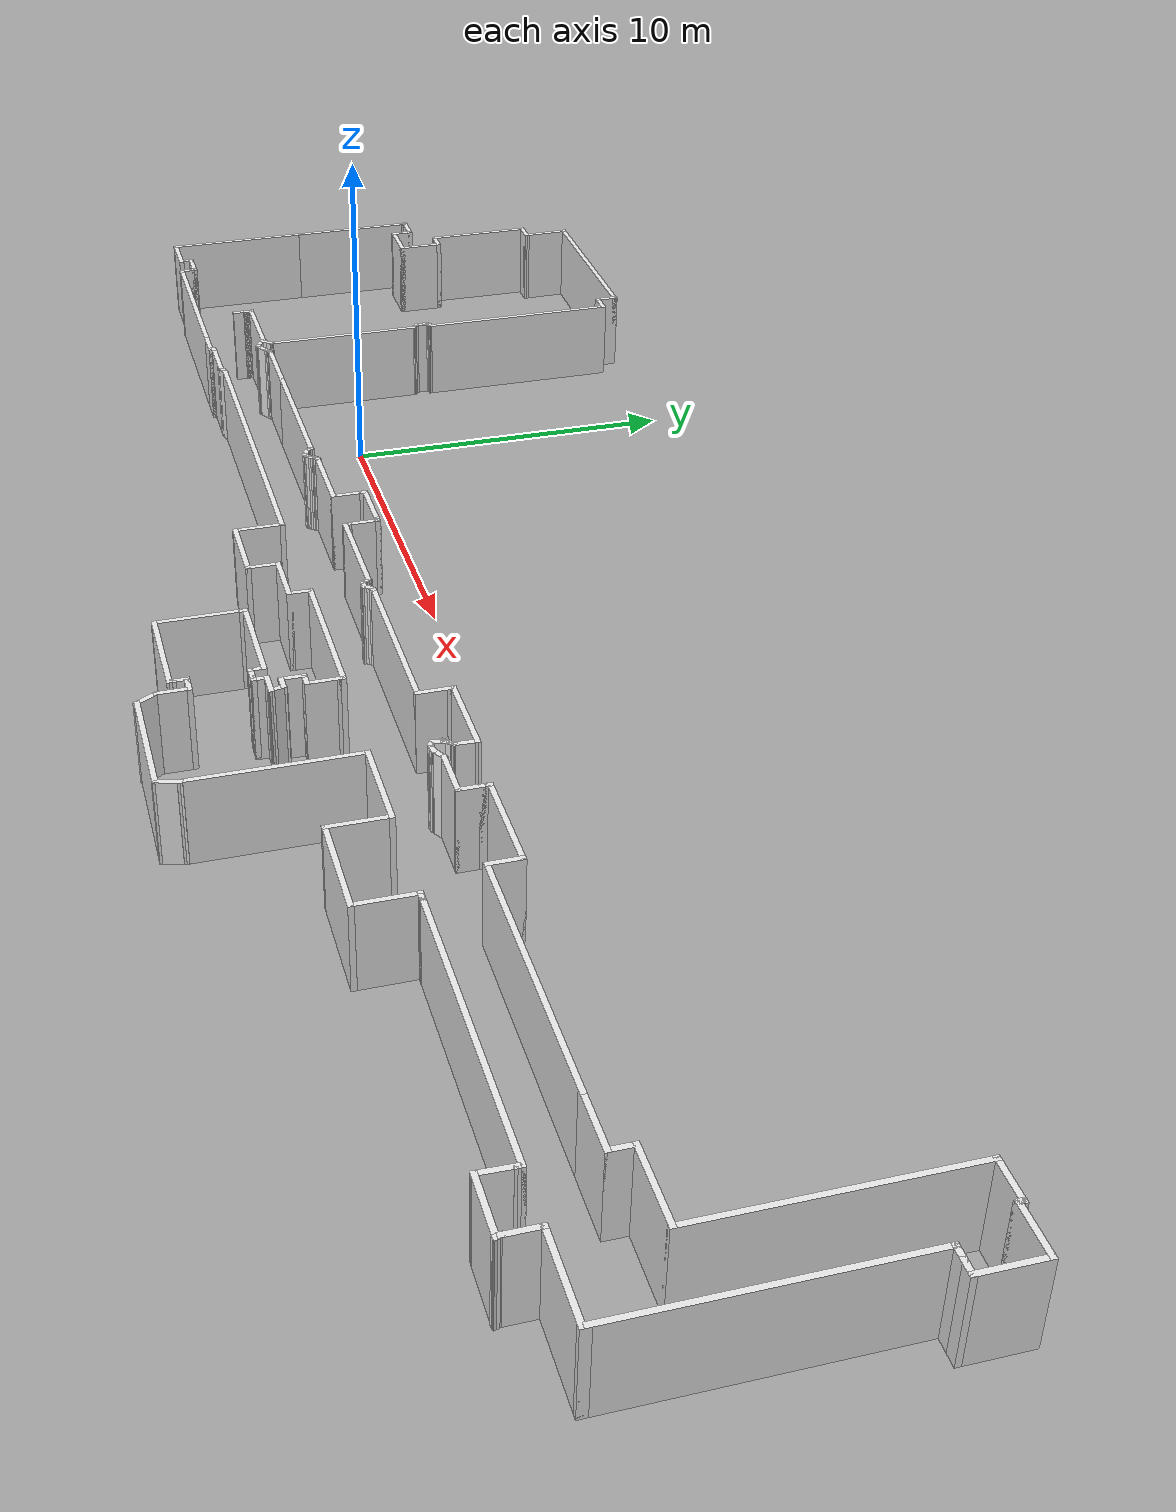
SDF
<?xml version='1.0'?>
<sdf version='1.4'>
  <model name='south_basement'>
    <pose>12.3228 0.447268 0 0 -0 0</pose>
    <link name='Wall_1'>
      <collision name='Wall_1_Collision'>
        <geometry>
          <box>
            <size>6.25 0.15 2.5</size>
          </box>
        </geometry>
        <pose>0 0 1.25 0 -0 0</pose>
      </collision>
      <visual name='Wall_1_Visual'>
        <pose>0 0 1.25 0 -0 0</pose>
        <geometry>
          <box>
            <size>6.25 0.15 2.5</size>
          </box>
        </geometry>
        <material>
          <script>
            <uri>file://media/materials/scripts/gazebo.material</uri>
            <name>Gazebo/White</name>
          </script>
          <ambient>1 1 1 1</ambient>
        </material>
      </visual>
      <pose>-19.9496 9.58415 0 0 -0 0</pose>
    </link>
    <link name='Wall_10'>
      <collision name='Wall_10_Collision'>
        <geometry>
          <box>
            <size>0.25 0.15 2.5</size>
          </box>
        </geometry>
        <pose>0 0 1.25 0 -0 0</pose>
      </collision>
      <visual name='Wall_10_Visual'>
        <pose>0 0 1.25 0 -0 0</pose>
        <geometry>
          <box>
            <size>0.25 0.15 2.5</size>
          </box>
        </geometry>
        <material>
          <script>
            <uri>file://media/materials/scripts/gazebo.material</uri>
            <name>Gazebo/White</name>
          </script>
          <ambient>1 1 1 1</ambient>
        </material>
      </visual>
      <pose>-16.4315 2.82291 0 0 0 -2.35619</pose>
    </link>
    <link name='Wall_100'>
      <collision name='Wall_100_Collision'>
        <geometry>
          <box>
            <size>1.5 0.15 2.5</size>
          </box>
        </geometry>
        <pose>0 0 1.25 0 -0 0</pose>
      </collision>
      <visual name='Wall_100_Visual'>
        <pose>0 0 1.25 0 -0 0</pose>
        <geometry>
          <box>
            <size>1.5 0.15 2.5</size>
          </box>
        </geometry>
        <material>
          <script>
            <uri>file://media/materials/scripts/gazebo.material</uri>
            <name>Gazebo/White</name>
          </script>
          <ambient>1 1 1 1</ambient>
        </material>
      </visual>
      <pose>24.5122 4.41793 0 0 -0 0</pose>
    </link>
    <link name='Wall_101'>
      <collision name='Wall_101_Collision'>
        <geometry>
          <box>
            <size>1.75 0.15 2.5</size>
          </box>
        </geometry>
        <pose>0 0 1.25 0 -0 0</pose>
      </collision>
      <visual name='Wall_101_Visual'>
        <pose>0 0 1.25 0 -0 0</pose>
        <geometry>
          <box>
            <size>1.75 0.15 2.5</size>
          </box>
        </geometry>
        <material>
          <script>
            <uri>file://media/materials/scripts/gazebo.material</uri>
            <name>Gazebo/White</name>
          </script>
          <ambient>1 1 1 1</ambient>
        </material>
      </visual>
      <pose>25.1872 3.61794 0 0 0 -1.5708</pose>
    </link>
    <link name='Wall_102'>
      <collision name='Wall_102_Collision'>
        <geometry>
          <box>
            <size>0.5 0.15 2.5</size>
          </box>
        </geometry>
        <pose>0 0 1.25 0 -0 0</pose>
      </collision>
      <visual name='Wall_102_Visual'>
        <pose>0 0 1.25 0 -0 0</pose>
        <geometry>
          <box>
            <size>0.5 0.15 2.5</size>
          </box>
        </geometry>
        <material>
          <script>
            <uri>file://media/materials/scripts/gazebo.material</uri>
            <name>Gazebo/White</name>
          </script>
          <ambient>1 1 1 1</ambient>
        </material>
      </visual>
      <pose>25.0122 2.81793 0 0 -0 3.14159</pose>
    </link>
    <link name='Wall_103'>
      <collision name='Wall_103_Collision'>
        <geometry>
          <box>
            <size>0.5 0.15 2.5</size>
          </box>
        </geometry>
        <pose>0 0 1.25 0 -0 0</pose>
      </collision>
      <visual name='Wall_103_Visual'>
        <pose>0 0 1.25 0 -0 0</pose>
        <geometry>
          <box>
            <size>0.5 0.15 2.5</size>
          </box>
        </geometry>
        <material>
          <script>
            <uri>file://media/materials/scripts/gazebo.material</uri>
            <name>Gazebo/White</name>
          </script>
          <ambient>1 1 1 1</ambient>
        </material>
      </visual>
      <pose>24.6622 2.81793 0 0 -0 3.14159</pose>
    </link>
    <link name='Wall_104'>
      <collision name='Wall_104_Collision'>
        <geometry>
          <box>
            <size>7.25 0.15 2.5</size>
          </box>
        </geometry>
        <pose>0 0 1.25 0 -0 0</pose>
      </collision>
      <visual name='Wall_104_Visual'>
        <pose>0 0 1.25 0 -0 0</pose>
        <geometry>
          <box>
            <size>7.25 0.15 2.5</size>
          </box>
        </geometry>
        <material>
          <script>
            <uri>file://media/materials/scripts/gazebo.material</uri>
            <name>Gazebo/White</name>
          </script>
          <ambient>1 1 1 1</ambient>
        </material>
      </visual>
      <pose>24.4872 -0.732065 0 0 0 -1.5708</pose>
    </link>
    <link name='Wall_105'>
      <collision name='Wall_105_Collision'>
        <geometry>
          <box>
            <size>0.25 0.15 2.5</size>
          </box>
        </geometry>
        <pose>0 0 1.25 0 -0 0</pose>
      </collision>
      <visual name='Wall_105_Visual'>
        <pose>0 0 1.25 0 -0 0</pose>
        <geometry>
          <box>
            <size>0.25 0.15 2.5</size>
          </box>
        </geometry>
        <material>
          <script>
            <uri>file://media/materials/scripts/gazebo.material</uri>
            <name>Gazebo/White</name>
          </script>
          <ambient>1 1 1 1</ambient>
        </material>
      </visual>
      <pose>24.4872 -4.33207 0 0 0 -1.5708</pose>
    </link>
    <link name='Wall_106'>
      <collision name='Wall_106_Collision'>
        <geometry>
          <box>
            <size>2.5 0.15 2.5</size>
          </box>
        </geometry>
        <pose>0 0 1.25 0 -0 0</pose>
      </collision>
      <visual name='Wall_106_Visual'>
        <pose>0 0 1.25 0 -0 0</pose>
        <geometry>
          <box>
            <size>2.5 0.15 2.5</size>
          </box>
        </geometry>
        <material>
          <script>
            <uri>file://media/materials/scripts/gazebo.material</uri>
            <name>Gazebo/White</name>
          </script>
          <ambient>1 1 1 1</ambient>
        </material>
      </visual>
      <pose>23.3122 -4.38206 0 0 -0 3.14159</pose>
    </link>
    <link name='Wall_107'>
      <collision name='Wall_107_Collision'>
        <geometry>
          <box>
            <size>1 0.15 2.5</size>
          </box>
        </geometry>
        <pose>0 0 1.25 0 -0 0</pose>
      </collision>
      <visual name='Wall_107_Visual'>
        <pose>0 0 1.25 0 -0 0</pose>
        <geometry>
          <box>
            <size>1 0.15 2.5</size>
          </box>
        </geometry>
        <material>
          <script>
            <uri>file://media/materials/scripts/gazebo.material</uri>
            <name>Gazebo/White</name>
          </script>
          <ambient>1 1 1 1</ambient>
        </material>
      </visual>
      <pose>22.1372 -4.80706 0 0 0 -1.5708</pose>
    </link>
    <link name='Wall_108'>
      <collision name='Wall_108_Collision'>
        <geometry>
          <box>
            <size>0.25 0.15 2.5</size>
          </box>
        </geometry>
        <pose>0 0 1.25 0 -0 0</pose>
      </collision>
      <visual name='Wall_108_Visual'>
        <pose>0 0 1.25 0 -0 0</pose>
        <geometry>
          <box>
            <size>0.25 0.15 2.5</size>
          </box>
        </geometry>
        <material>
          <script>
            <uri>file://media/materials/scripts/gazebo.material</uri>
            <name>Gazebo/White</name>
          </script>
          <ambient>1 1 1 1</ambient>
        </material>
      </visual>
      <pose>22.1501 -5.28036 0 0 0 -1.309</pose>
    </link>
    <link name='Wall_109'>
      <collision name='Wall_109_Collision'>
        <geometry>
          <box>
            <size>1.75 0.15 2.5</size>
          </box>
        </geometry>
        <pose>0 0 1.25 0 -0 0</pose>
      </collision>
      <visual name='Wall_109_Visual'>
        <pose>0 0 1.25 0 -0 0</pose>
        <geometry>
          <box>
            <size>1.75 0.15 2.5</size>
          </box>
        </geometry>
        <material>
          <script>
            <uri>file://media/materials/scripts/gazebo.material</uri>
            <name>Gazebo/White</name>
          </script>
          <ambient>1 1 1 1</ambient>
        </material>
      </visual>
      <pose>21.3631 -5.32866 0 0 -0 3.14159</pose>
    </link>
    <link name='Wall_11'>
      <collision name='Wall_11_Collision'>
        <geometry>
          <box>
            <size>0.25 0.15 2.5</size>
          </box>
        </geometry>
        <pose>0 0 1.25 0 -0 0</pose>
      </collision>
      <visual name='Wall_11_Visual'>
        <pose>0 0 1.25 0 -0 0</pose>
        <geometry>
          <box>
            <size>0.25 0.15 2.5</size>
          </box>
        </geometry>
        <material>
          <script>
            <uri>file://media/materials/scripts/gazebo.material</uri>
            <name>Gazebo/White</name>
          </script>
          <ambient>1 1 1 1</ambient>
        </material>
      </visual>
      <pose>-16.5022 2.7522 0 0 0 -2.35619</pose>
    </link>
    <link name='Wall_110'>
      <collision name='Wall_110_Collision'>
        <geometry>
          <box>
            <size>0.15 0.15 2.5</size>
          </box>
        </geometry>
        <pose>0 0 1.25 0 -0 0</pose>
      </collision>
      <visual name='Wall_110_Visual'>
        <pose>0 0 1.25 0 -0 0</pose>
        <geometry>
          <box>
            <size>0.15 0.15 2.5</size>
          </box>
        </geometry>
        <material>
          <script>
            <uri>file://media/materials/scripts/gazebo.material</uri>
            <name>Gazebo/White</name>
          </script>
          <ambient>1 1 1 1</ambient>
        </material>
      </visual>
      <pose>20.5631 -5.32866 0 0 -0 0</pose>
    </link>
    <link name='Wall_111'>
      <collision name='Wall_111_Collision'>
        <geometry>
          <box>
            <size>1 0.15 2.5</size>
          </box>
        </geometry>
        <pose>0 0 1.25 0 -0 0</pose>
      </collision>
      <visual name='Wall_111_Visual'>
        <pose>0 0 1.25 0 -0 0</pose>
        <geometry>
          <box>
            <size>1 0.15 2.5</size>
          </box>
        </geometry>
        <material>
          <script>
            <uri>file://media/materials/scripts/gazebo.material</uri>
            <name>Gazebo/White</name>
          </script>
          <ambient>1 1 1 1</ambient>
        </material>
      </visual>
      <pose>20.5763 -4.90366 0 0 -0 1.53969</pose>
    </link>
    <link name='Wall_114'>
      <collision name='Wall_114_Collision'>
        <geometry>
          <box>
            <size>0.25 0.15 2.5</size>
          </box>
        </geometry>
        <pose>0 0 1.25 0 -0 0</pose>
      </collision>
      <visual name='Wall_114_Visual'>
        <pose>0 0 1.25 0 -0 0</pose>
        <geometry>
          <box>
            <size>0.25 0.15 2.5</size>
          </box>
        </geometry>
        <material>
          <script>
            <uri>file://media/materials/scripts/gazebo.material</uri>
            <name>Gazebo/White</name>
          </script>
          <ambient>1 1 1 1</ambient>
        </material>
      </visual>
      <pose>20.5895 -4.42866 0 0 -0 1.5708</pose>
    </link>
    <link name='Wall_115'>
      <collision name='Wall_115_Collision'>
        <geometry>
          <box>
            <size>8.25 0.15 2.5</size>
          </box>
        </geometry>
        <pose>0 0 1.25 0 -0 0</pose>
      </collision>
      <visual name='Wall_115_Visual'>
        <pose>0 0 1.25 0 -0 0</pose>
        <geometry>
          <box>
            <size>8.25 0.15 2.5</size>
          </box>
        </geometry>
        <material>
          <script>
            <uri>file://media/materials/scripts/gazebo.material</uri>
            <name>Gazebo/White</name>
          </script>
          <ambient>1 1 1 1</ambient>
        </material>
      </visual>
      <pose>16.5395 -4.37866 0 0 -0 3.14159</pose>
    </link>
    <link name='Wall_116'>
      <collision name='Wall_116_Collision'>
        <geometry>
          <box>
            <size>0.25 0.15 2.5</size>
          </box>
        </geometry>
        <pose>0 0 1.25 0 -0 0</pose>
      </collision>
      <visual name='Wall_116_Visual'>
        <pose>0 0 1.25 0 -0 0</pose>
        <geometry>
          <box>
            <size>0.25 0.15 2.5</size>
          </box>
        </geometry>
        <material>
          <script>
            <uri>file://media/materials/scripts/gazebo.material</uri>
            <name>Gazebo/White</name>
          </script>
          <ambient>1 1 1 1</ambient>
        </material>
      </visual>
      <pose>12.4395 -4.37866 0 0 -0 3.14159</pose>
    </link>
    <link name='Wall_117'>
      <collision name='Wall_117_Collision'>
        <geometry>
          <box>
            <size>0.25 0.15 2.5</size>
          </box>
        </geometry>
        <pose>0 0 1.25 0 -0 0</pose>
      </collision>
      <visual name='Wall_117_Visual'>
        <pose>0 0 1.25 0 -0 0</pose>
        <geometry>
          <box>
            <size>0.25 0.15 2.5</size>
          </box>
        </geometry>
        <material>
          <script>
            <uri>file://media/materials/scripts/gazebo.material</uri>
            <name>Gazebo/White</name>
          </script>
          <ambient>1 1 1 1</ambient>
        </material>
      </visual>
      <pose>12.3395 -4.37866 0 0 -0 3.14159</pose>
    </link>
    <link name='Wall_118'>
      <collision name='Wall_118_Collision'>
        <geometry>
          <box>
            <size>1.75 0.15 2.5</size>
          </box>
        </geometry>
        <pose>0 0 1.25 0 -0 0</pose>
      </collision>
      <visual name='Wall_118_Visual'>
        <pose>0 0 1.25 0 -0 0</pose>
        <geometry>
          <box>
            <size>1.75 0.15 2.5</size>
          </box>
        </geometry>
        <material>
          <script>
            <uri>file://media/materials/scripts/gazebo.material</uri>
            <name>Gazebo/White</name>
          </script>
          <ambient>1 1 1 1</ambient>
        </material>
      </visual>
      <pose>12.2895 -5.17866 0 0 0 -1.5708</pose>
    </link>
    <link name='Wall_119'>
      <collision name='Wall_119_Collision'>
        <geometry>
          <box>
            <size>3 0.15 2.5</size>
          </box>
        </geometry>
        <pose>0 0 1.25 0 -0 0</pose>
      </collision>
      <visual name='Wall_119_Visual'>
        <pose>0 0 1.25 0 -0 0</pose>
        <geometry>
          <box>
            <size>3 0.15 2.5</size>
          </box>
        </geometry>
        <material>
          <script>
            <uri>file://media/materials/scripts/gazebo.material</uri>
            <name>Gazebo/White</name>
          </script>
          <ambient>1 1 1 1</ambient>
        </material>
      </visual>
      <pose>10.8645 -5.97866 0 0 -0 3.14159</pose>
    </link>
    <link name='Wall_120'>
      <collision name='Wall_120_Collision'>
        <geometry>
          <box>
            <size>1.75 0.15 2.5</size>
          </box>
        </geometry>
        <pose>0 0 1.25 0 -0 0</pose>
      </collision>
      <visual name='Wall_120_Visual'>
        <pose>0 0 1.25 0 -0 0</pose>
        <geometry>
          <box>
            <size>1.75 0.15 2.5</size>
          </box>
        </geometry>
        <material>
          <script>
            <uri>file://media/materials/scripts/gazebo.material</uri>
            <name>Gazebo/White</name>
          </script>
          <ambient>1 1 1 1</ambient>
        </material>
      </visual>
      <pose>9.43951 -5.17866 0 0 -0 1.5708</pose>
    </link>
    <link name='Wall_121'>
      <collision name='Wall_121_Collision'>
        <geometry>
          <box>
            <size>2.75 0.15 2.5</size>
          </box>
        </geometry>
        <pose>0 0 1.25 0 -0 0</pose>
      </collision>
      <visual name='Wall_121_Visual'>
        <pose>0 0 1.25 0 -0 0</pose>
        <geometry>
          <box>
            <size>2.75 0.15 2.5</size>
          </box>
        </geometry>
        <material>
          <script>
            <uri>file://media/materials/scripts/gazebo.material</uri>
            <name>Gazebo/White</name>
          </script>
          <ambient>1 1 1 1</ambient>
        </material>
      </visual>
      <pose>8.13951 -4.37866 0 0 -0 3.14159</pose>
    </link>
    <link name='Wall_123'>
      <collision name='Wall_123_Collision'>
        <geometry>
          <box>
            <size>4.75 0.15 2.5</size>
          </box>
        </geometry>
        <pose>0 0 1.25 0 -0 0</pose>
      </collision>
      <visual name='Wall_123_Visual'>
        <pose>0 0 1.25 0 -0 0</pose>
        <geometry>
          <box>
            <size>4.75 0.15 2.5</size>
          </box>
        </geometry>
        <material>
          <script>
            <uri>file://media/materials/scripts/gazebo.material</uri>
            <name>Gazebo/White</name>
          </script>
          <ambient>1 1 1 1</ambient>
        </material>
      </visual>
      <pose>6.83951 -6.67866 0 0 0 -1.5708</pose>
    </link>
    <link name='Wall_124'>
      <collision name='Wall_124_Collision'>
        <geometry>
          <box>
            <size>0.75 0.15 2.5</size>
          </box>
        </geometry>
        <pose>0 0 1.25 0 -0 0</pose>
      </collision>
      <visual name='Wall_124_Visual'>
        <pose>0 0 1.25 0 -0 0</pose>
        <geometry>
          <box>
            <size>0.75 0.15 2.5</size>
          </box>
        </geometry>
        <material>
          <script>
            <uri>file://media/materials/scripts/gazebo.material</uri>
            <name>Gazebo/White</name>
          </script>
          <ambient>1 1 1 1</ambient>
        </material>
      </visual>
      <pose>6.76187 -9.26844 0 0 0 -1.8326</pose>
    </link>
    <link name='Wall_125'>
      <collision name='Wall_125_Collision'>
        <geometry>
          <box>
            <size>3.5 0.15 2.5</size>
          </box>
        </geometry>
        <pose>0 0 1.25 0 -0 0</pose>
      </collision>
      <visual name='Wall_125_Visual'>
        <pose>0 0 1.25 0 -0 0</pose>
        <geometry>
          <box>
            <size>3.5 0.15 2.5</size>
          </box>
        </geometry>
        <material>
          <script>
            <uri>file://media/materials/scripts/gazebo.material</uri>
            <name>Gazebo/White</name>
          </script>
          <ambient>1 1 1 1</ambient>
        </material>
      </visual>
      <pose>5.00922 -9.55821 0 0 -0 3.14159</pose>
    </link>
    <link name='Wall_126'>
      <collision name='Wall_126_Collision'>
        <geometry>
          <box>
            <size>0.75 0.15 2.5</size>
          </box>
        </geometry>
        <pose>0 0 1.25 0 -0 0</pose>
      </collision>
      <visual name='Wall_126_Visual'>
        <pose>0 0 1.25 0 -0 0</pose>
        <geometry>
          <box>
            <size>0.75 0.15 2.5</size>
          </box>
        </geometry>
        <material>
          <script>
            <uri>file://media/materials/scripts/gazebo.material</uri>
            <name>Gazebo/White</name>
          </script>
          <ambient>1 1 1 1</ambient>
        </material>
      </visual>
      <pose>3.18422 -9.29841 0 0 -0 2.0944</pose>
    </link>
    <link name='Wall_127'>
      <collision name='Wall_127_Collision'>
        <geometry>
          <box>
            <size>1 0.15 2.5</size>
          </box>
        </geometry>
        <pose>0 0 1.25 0 -0 0</pose>
      </collision>
      <visual name='Wall_127_Visual'>
        <pose>0 0 1.25 0 -0 0</pose>
        <geometry>
          <box>
            <size>1 0.15 2.5</size>
          </box>
        </geometry>
        <material>
          <script>
            <uri>file://media/materials/scripts/gazebo.material</uri>
            <name>Gazebo/White</name>
          </script>
          <ambient>1 1 1 1</ambient>
        </material>
      </visual>
      <pose>3.03422 -8.6136 0 0 -0 1.5708</pose>
    </link>
    <link name='Wall_128'>
      <collision name='Wall_128_Collision'>
        <geometry>
          <box>
            <size>0.5 0.15 2.5</size>
          </box>
        </geometry>
        <pose>0 0 1.25 0 -0 0</pose>
      </collision>
      <visual name='Wall_128_Visual'>
        <pose>0 0 1.25 0 -0 0</pose>
        <geometry>
          <box>
            <size>0.5 0.15 2.5</size>
          </box>
        </geometry>
        <material>
          <script>
            <uri>file://media/materials/scripts/gazebo.material</uri>
            <name>Gazebo/White</name>
          </script>
          <ambient>1 1 1 1</ambient>
        </material>
      </visual>
      <pose>2.85922 -8.1886 0 0 -0 3.14159</pose>
    </link>
    <link name='Wall_129'>
      <collision name='Wall_129_Collision'>
        <geometry>
          <box>
            <size>0.25 0.15 2.5</size>
          </box>
        </geometry>
        <pose>0 0 1.25 0 -0 0</pose>
      </collision>
      <visual name='Wall_129_Visual'>
        <pose>0 0 1.25 0 -0 0</pose>
        <geometry>
          <box>
            <size>0.25 0.15 2.5</size>
          </box>
        </geometry>
        <material>
          <script>
            <uri>file://media/materials/scripts/gazebo.material</uri>
            <name>Gazebo/White</name>
          </script>
          <ambient>1 1 1 1</ambient>
        </material>
      </visual>
      <pose>2.63422 -8.1886 0 0 -0 3.14159</pose>
    </link>
    <link name='Wall_130'>
      <collision name='Wall_130_Collision'>
        <geometry>
          <box>
            <size>0.5 0.15 2.5</size>
          </box>
        </geometry>
        <pose>0 0 1.25 0 -0 0</pose>
      </collision>
      <visual name='Wall_130_Visual'>
        <pose>0 0 1.25 0 -0 0</pose>
        <geometry>
          <box>
            <size>0.5 0.15 2.5</size>
          </box>
        </geometry>
        <material>
          <script>
            <uri>file://media/materials/scripts/gazebo.material</uri>
            <name>Gazebo/White</name>
          </script>
          <ambient>1 1 1 1</ambient>
        </material>
      </visual>
      <pose>2.58422 -8.3636 0 0 0 -1.5708</pose>
    </link>
    <link name='Wall_131'>
      <collision name='Wall_131_Collision'>
        <geometry>
          <box>
            <size>0.25 0.15 2.5</size>
          </box>
        </geometry>
        <pose>0 0 1.25 0 -0 0</pose>
      </collision>
      <visual name='Wall_131_Visual'>
        <pose>0 0 1.25 0 -0 0</pose>
        <geometry>
          <box>
            <size>0.25 0.15 2.5</size>
          </box>
        </geometry>
        <material>
          <script>
            <uri>file://media/materials/scripts/gazebo.material</uri>
            <name>Gazebo/White</name>
          </script>
          <ambient>1 1 1 1</ambient>
        </material>
      </visual>
      <pose>2.58422 -8.5886 0 0 0 -1.5708</pose>
    </link>
    <link name='Wall_132'>
      <collision name='Wall_132_Collision'>
        <geometry>
          <box>
            <size>3 0.15 2.5</size>
          </box>
        </geometry>
        <pose>0 0 1.25 0 -0 0</pose>
      </collision>
      <visual name='Wall_132_Visual'>
        <pose>0 0 1.25 0 -0 0</pose>
        <geometry>
          <box>
            <size>3 0.15 2.5</size>
          </box>
        </geometry>
        <material>
          <script>
            <uri>file://media/materials/scripts/gazebo.material</uri>
            <name>Gazebo/White</name>
          </script>
          <ambient>1 1 1 1</ambient>
        </material>
      </visual>
      <pose>1.15922 -8.6386 0 0 -0 3.14159</pose>
    </link>
    <link name='Wall_133'>
      <collision name='Wall_133_Collision'>
        <geometry>
          <box>
            <size>2.5 0.15 2.5</size>
          </box>
        </geometry>
        <pose>0 0 1.25 0 -0 0</pose>
      </collision>
      <visual name='Wall_133_Visual'>
        <pose>0 0 1.25 0 -0 0</pose>
        <geometry>
          <box>
            <size>2.5 0.15 2.5</size>
          </box>
        </geometry>
        <material>
          <script>
            <uri>file://media/materials/scripts/gazebo.material</uri>
            <name>Gazebo/White</name>
          </script>
          <ambient>1 1 1 1</ambient>
        </material>
      </visual>
      <pose>-0.26578 -7.4636 0 0 -0 1.5708</pose>
    </link>
    <link name='Wall_134'>
      <collision name='Wall_134_Collision'>
        <geometry>
          <box>
            <size>0.25 0.15 2.5</size>
          </box>
        </geometry>
        <pose>0 0 1.25 0 -0 0</pose>
      </collision>
      <visual name='Wall_134_Visual'>
        <pose>0 0 1.25 0 -0 0</pose>
        <geometry>
          <box>
            <size>0.25 0.15 2.5</size>
          </box>
        </geometry>
        <material>
          <script>
            <uri>file://media/materials/scripts/gazebo.material</uri>
            <name>Gazebo/White</name>
          </script>
          <ambient>1 1 1 1</ambient>
        </material>
      </visual>
      <pose>-0.26578 -6.2386 0 0 -0 1.5708</pose>
    </link>
    <link name='Wall_135'>
      <collision name='Wall_135_Collision'>
        <geometry>
          <box>
            <size>3 0.15 2.5</size>
          </box>
        </geometry>
        <pose>0 0 1.25 0 -0 0</pose>
      </collision>
      <visual name='Wall_135_Visual'>
        <pose>0 0 1.25 0 -0 0</pose>
        <geometry>
          <box>
            <size>3 0.15 2.5</size>
          </box>
        </geometry>
        <material>
          <script>
            <uri>file://media/materials/scripts/gazebo.material</uri>
            <name>Gazebo/White</name>
          </script>
          <ambient>1 1 1 1</ambient>
        </material>
      </visual>
      <pose>1.15922 -6.1886 0 0 -0 0</pose>
    </link>
    <link name='Wall_136'>
      <collision name='Wall_136_Collision'>
        <geometry>
          <box>
            <size>0.5 0.15 2.5</size>
          </box>
        </geometry>
        <pose>0 0 1.25 0 -0 0</pose>
      </collision>
      <visual name='Wall_136_Visual'>
        <pose>0 0 1.25 0 -0 0</pose>
        <geometry>
          <box>
            <size>0.5 0.15 2.5</size>
          </box>
        </geometry>
        <material>
          <script>
            <uri>file://media/materials/scripts/gazebo.material</uri>
            <name>Gazebo/White</name>
          </script>
          <ambient>1 1 1 1</ambient>
        </material>
      </visual>
      <pose>2.58422 -6.3636 0 0 0 -1.5708</pose>
    </link>
    <link name='Wall_137'>
      <collision name='Wall_137_Collision'>
        <geometry>
          <box>
            <size>0.5 0.15 2.5</size>
          </box>
        </geometry>
        <pose>0 0 1.25 0 -0 0</pose>
      </collision>
      <visual name='Wall_137_Visual'>
        <pose>0 0 1.25 0 -0 0</pose>
        <geometry>
          <box>
            <size>0.5 0.15 2.5</size>
          </box>
        </geometry>
        <material>
          <script>
            <uri>file://media/materials/scripts/gazebo.material</uri>
            <name>Gazebo/White</name>
          </script>
          <ambient>1 1 1 1</ambient>
        </material>
      </visual>
      <pose>2.75922 -6.5386 0 0 -0 0</pose>
    </link>
    <link name='Wall_138'>
      <collision name='Wall_138_Collision'>
        <geometry>
          <box>
            <size>0.25 0.15 2.5</size>
          </box>
        </geometry>
        <pose>0 0 1.25 0 -0 0</pose>
      </collision>
      <visual name='Wall_138_Visual'>
        <pose>0 0 1.25 0 -0 0</pose>
        <geometry>
          <box>
            <size>0.25 0.15 2.5</size>
          </box>
        </geometry>
        <material>
          <script>
            <uri>file://media/materials/scripts/gazebo.material</uri>
            <name>Gazebo/White</name>
          </script>
          <ambient>1 1 1 1</ambient>
        </material>
      </visual>
      <pose>2.98422 -6.5386 0 0 -0 0</pose>
    </link>
    <link name='Wall_139'>
      <collision name='Wall_139_Collision'>
        <geometry>
          <box>
            <size>0.5 0.15 2.5</size>
          </box>
        </geometry>
        <pose>0 0 1.25 0 -0 0</pose>
      </collision>
      <visual name='Wall_139_Visual'>
        <pose>0 0 1.25 0 -0 0</pose>
        <geometry>
          <box>
            <size>0.5 0.15 2.5</size>
          </box>
        </geometry>
        <material>
          <script>
            <uri>file://media/materials/scripts/gazebo.material</uri>
            <name>Gazebo/White</name>
          </script>
          <ambient>1 1 1 1</ambient>
        </material>
      </visual>
      <pose>3.03422 -6.3636 0 0 -0 1.5708</pose>
    </link>
    <link name='Wall_14'>
      <collision name='Wall_14_Collision'>
        <geometry>
          <box>
            <size>0.5 0.15 2.5</size>
          </box>
        </geometry>
        <pose>0 0 1.25 0 -0 0</pose>
      </collision>
      <visual name='Wall_14_Visual'>
        <pose>0 0 1.25 0 -0 0</pose>
        <geometry>
          <box>
            <size>0.5 0.15 2.5</size>
          </box>
        </geometry>
        <material>
          <script>
            <uri>file://media/materials/scripts/gazebo.material</uri>
            <name>Gazebo/White</name>
          </script>
          <ambient>1 1 1 1</ambient>
        </material>
      </visual>
      <pose>-16.4669 2.61255 0 0 0 -1.5708</pose>
    </link>
    <link name='Wall_140'>
      <collision name='Wall_140_Collision'>
        <geometry>
          <box>
            <size>0.75 0.15 2.5</size>
          </box>
        </geometry>
        <pose>0 0 1.25 0 -0 0</pose>
      </collision>
      <visual name='Wall_140_Visual'>
        <pose>0 0 1.25 0 -0 0</pose>
        <geometry>
          <box>
            <size>0.75 0.15 2.5</size>
          </box>
        </geometry>
        <material>
          <script>
            <uri>file://media/materials/scripts/gazebo.material</uri>
            <name>Gazebo/White</name>
          </script>
          <ambient>1 1 1 1</ambient>
        </material>
      </visual>
      <pose>3.33422 -6.1886 0 0 -0 0</pose>
    </link>
    <link name='Wall_141'>
      <collision name='Wall_141_Collision'>
        <geometry>
          <box>
            <size>0.5 0.15 2.5</size>
          </box>
        </geometry>
        <pose>0 0 1.25 0 -0 0</pose>
      </collision>
      <visual name='Wall_141_Visual'>
        <pose>0 0 1.25 0 -0 0</pose>
        <geometry>
          <box>
            <size>0.5 0.15 2.5</size>
          </box>
        </geometry>
        <material>
          <script>
            <uri>file://media/materials/scripts/gazebo.material</uri>
            <name>Gazebo/White</name>
          </script>
          <ambient>1 1 1 1</ambient>
        </material>
      </visual>
      <pose>3.58893 -6.01956 0 0 -0 1.8326</pose>
    </link>
    <link name='Wall_142'>
      <collision name='Wall_142_Collision'>
        <geometry>
          <box>
            <size>0.5 0.15 2.5</size>
          </box>
        </geometry>
        <pose>0 0 1.25 0 -0 0</pose>
      </collision>
      <visual name='Wall_142_Visual'>
        <pose>0 0 1.25 0 -0 0</pose>
        <geometry>
          <box>
            <size>0.5 0.15 2.5</size>
          </box>
        </geometry>
        <material>
          <script>
            <uri>file://media/materials/scripts/gazebo.material</uri>
            <name>Gazebo/White</name>
          </script>
          <ambient>1 1 1 1</ambient>
        </material>
      </visual>
      <pose>3.36863 -5.85052 0 0 -0 3.14159</pose>
    </link>
    <link name='Wall_143'>
      <collision name='Wall_143_Collision'>
        <geometry>
          <box>
            <size>0.75 0.15 2.5</size>
          </box>
        </geometry>
        <pose>0 0 1.25 0 -0 0</pose>
      </collision>
      <visual name='Wall_143_Visual'>
        <pose>0 0 1.25 0 -0 0</pose>
        <geometry>
          <box>
            <size>0.75 0.15 2.5</size>
          </box>
        </geometry>
        <material>
          <script>
            <uri>file://media/materials/scripts/gazebo.material</uri>
            <name>Gazebo/White</name>
          </script>
          <ambient>1 1 1 1</ambient>
        </material>
      </visual>
      <pose>3.19363 -5.55052 0 0 -0 1.5708</pose>
    </link>
    <link name='Wall_144'>
      <collision name='Wall_144_Collision'>
        <geometry>
          <box>
            <size>0.5 0.15 2.5</size>
          </box>
        </geometry>
        <pose>0 0 1.25 0 -0 0</pose>
      </collision>
      <visual name='Wall_144_Visual'>
        <pose>0 0 1.25 0 -0 0</pose>
        <geometry>
          <box>
            <size>0.5 0.15 2.5</size>
          </box>
        </geometry>
        <material>
          <script>
            <uri>file://media/materials/scripts/gazebo.material</uri>
            <name>Gazebo/White</name>
          </script>
          <ambient>1 1 1 1</ambient>
        </material>
      </visual>
      <pose>3.36863 -5.25052 0 0 -0 0</pose>
    </link>
    <link name='Wall_145'>
      <collision name='Wall_145_Collision'>
        <geometry>
          <box>
            <size>1 0.15 2.5</size>
          </box>
        </geometry>
        <pose>0 0 1.25 0 -0 0</pose>
      </collision>
      <visual name='Wall_145_Visual'>
        <pose>0 0 1.25 0 -0 0</pose>
        <geometry>
          <box>
            <size>1 0.15 2.5</size>
          </box>
        </geometry>
        <material>
          <script>
            <uri>file://media/materials/scripts/gazebo.material</uri>
            <name>Gazebo/White</name>
          </script>
          <ambient>1 1 1 1</ambient>
        </material>
      </visual>
      <pose>3.54363 -4.82552 0 0 -0 1.5708</pose>
    </link>
    <link name='Wall_147'>
      <collision name='Wall_147_Collision'>
        <geometry>
          <box>
            <size>0.25 0.15 2.5</size>
          </box>
        </geometry>
        <pose>0 0 1.25 0 -0 0</pose>
      </collision>
      <visual name='Wall_147_Visual'>
        <pose>0 0 1.25 0 -0 0</pose>
        <geometry>
          <box>
            <size>0.25 0.15 2.5</size>
          </box>
        </geometry>
        <material>
          <script>
            <uri>file://media/materials/scripts/gazebo.material</uri>
            <name>Gazebo/White</name>
          </script>
          <ambient>1 1 1 1</ambient>
        </material>
      </visual>
      <pose>3.54363 -4.35052 0 0 -0 1.5708</pose>
    </link>
    <link name='Wall_148'>
      <collision name='Wall_148_Collision'>
        <geometry>
          <box>
            <size>4.5 0.15 2.5</size>
          </box>
        </geometry>
        <pose>0 0 1.25 0 -0 0</pose>
      </collision>
      <visual name='Wall_148_Visual'>
        <pose>0 0 1.25 0 -0 0</pose>
        <geometry>
          <box>
            <size>4.5 0.15 2.5</size>
          </box>
        </geometry>
        <material>
          <script>
            <uri>file://media/materials/scripts/gazebo.material</uri>
            <name>Gazebo/White</name>
          </script>
          <ambient>1 1 1 1</ambient>
        </material>
      </visual>
      <pose>1.36863 -4.30052 0 0 -0 3.14159</pose>
    </link>
    <link name='Wall_149'>
      <collision name='Wall_149_Collision'>
        <geometry>
          <box>
            <size>0.75 0.15 2.5</size>
          </box>
        </geometry>
        <pose>0 0 1.25 0 -0 0</pose>
      </collision>
      <visual name='Wall_149_Visual'>
        <pose>0 0 1.25 0 -0 0</pose>
        <geometry>
          <box>
            <size>0.75 0.15 2.5</size>
          </box>
        </geometry>
        <material>
          <script>
            <uri>file://media/materials/scripts/gazebo.material</uri>
            <name>Gazebo/White</name>
          </script>
          <ambient>1 1 1 1</ambient>
        </material>
      </visual>
      <pose>-0.806367 -4.60052 0 0 0 -1.5708</pose>
    </link>
    <link name='Wall_15'>
      <collision name='Wall_15_Collision'>
        <geometry>
          <box>
            <size>0.25 0.15 2.5</size>
          </box>
        </geometry>
        <pose>0 0 1.25 0 -0 0</pose>
      </collision>
      <visual name='Wall_15_Visual'>
        <pose>0 0 1.25 0 -0 0</pose>
        <geometry>
          <box>
            <size>0.25 0.15 2.5</size>
          </box>
        </geometry>
        <material>
          <script>
            <uri>file://media/materials/scripts/gazebo.material</uri>
            <name>Gazebo/White</name>
          </script>
          <ambient>1 1 1 1</ambient>
        </material>
      </visual>
      <pose>-16.4315 2.4022 0 0 0 -0.785398</pose>
    </link>
    <link name='Wall_150'>
      <collision name='Wall_150_Collision'>
        <geometry>
          <box>
            <size>1.75 0.15 2.5</size>
          </box>
        </geometry>
        <pose>0 0 1.25 0 -0 0</pose>
      </collision>
      <visual name='Wall_150_Visual'>
        <pose>0 0 1.25 0 -0 0</pose>
        <geometry>
          <box>
            <size>1.75 0.15 2.5</size>
          </box>
        </geometry>
        <material>
          <script>
            <uri>file://media/materials/scripts/gazebo.material</uri>
            <name>Gazebo/White</name>
          </script>
          <ambient>1 1 1 1</ambient>
        </material>
      </visual>
      <pose>-1.60637 -4.90052 0 0 -0 3.14159</pose>
    </link>
    <link name='Wall_151'>
      <collision name='Wall_151_Collision'>
        <geometry>
          <box>
            <size>1 0.15 2.5</size>
          </box>
        </geometry>
        <pose>0 0 1.25 0 -0 0</pose>
      </collision>
      <visual name='Wall_151_Visual'>
        <pose>0 0 1.25 0 -0 0</pose>
        <geometry>
          <box>
            <size>1 0.15 2.5</size>
          </box>
        </geometry>
        <material>
          <script>
            <uri>file://media/materials/scripts/gazebo.material</uri>
            <name>Gazebo/White</name>
          </script>
          <ambient>1 1 1 1</ambient>
        </material>
      </visual>
      <pose>-2.40637 -5.32552 0 0 0 -1.5708</pose>
    </link>
    <link name='Wall_152'>
      <collision name='Wall_152_Collision'>
        <geometry>
          <box>
            <size>2.25 0.15 2.5</size>
          </box>
        </geometry>
        <pose>0 0 1.25 0 -0 0</pose>
      </collision>
      <visual name='Wall_152_Visual'>
        <pose>0 0 1.25 0 -0 0</pose>
        <geometry>
          <box>
            <size>2.25 0.15 2.5</size>
          </box>
        </geometry>
        <material>
          <script>
            <uri>file://media/materials/scripts/gazebo.material</uri>
            <name>Gazebo/White</name>
          </script>
          <ambient>1 1 1 1</ambient>
        </material>
      </visual>
      <pose>-3.45637 -5.75052 0 0 -0 3.14159</pose>
    </link>
    <link name='Wall_153'>
      <collision name='Wall_153_Collision'>
        <geometry>
          <box>
            <size>1.5 0.15 2.5</size>
          </box>
        </geometry>
        <pose>0 0 1.25 0 -0 0</pose>
      </collision>
      <visual name='Wall_153_Visual'>
        <pose>0 0 1.25 0 -0 0</pose>
        <geometry>
          <box>
            <size>1.5 0.15 2.5</size>
          </box>
        </geometry>
        <material>
          <script>
            <uri>file://media/materials/scripts/gazebo.material</uri>
            <name>Gazebo/White</name>
          </script>
          <ambient>1 1 1 1</ambient>
        </material>
      </visual>
      <pose>-4.50637 -5.07552 0 0 -0 1.5708</pose>
    </link>
    <link name='Wall_155'>
      <collision name='Wall_155_Collision'>
        <geometry>
          <box>
            <size>10.25 0.15 2.5</size>
          </box>
        </geometry>
        <pose>0 0 1.25 0 -0 0</pose>
      </collision>
      <visual name='Wall_155_Visual'>
        <pose>0 0 1.25 0 -0 0</pose>
        <geometry>
          <box>
            <size>10.25 0.15 2.5</size>
          </box>
        </geometry>
        <material>
          <script>
            <uri>file://media/materials/scripts/gazebo.material</uri>
            <name>Gazebo/White</name>
          </script>
          <ambient>1 1 1 1</ambient>
        </material>
      </visual>
      <pose>-9.55637 -4.40052 0 0 -0 3.14159</pose>
    </link>
    <link name='Wall_156'>
      <collision name='Wall_156_Collision'>
        <geometry>
          <box>
            <size>0.5 0.15 2.5</size>
          </box>
        </geometry>
        <pose>0 0 1.25 0 -0 0</pose>
      </collision>
      <visual name='Wall_156_Visual'>
        <pose>0 0 1.25 0 -0 0</pose>
        <geometry>
          <box>
            <size>0.5 0.15 2.5</size>
          </box>
        </geometry>
        <material>
          <script>
            <uri>file://media/materials/scripts/gazebo.material</uri>
            <name>Gazebo/White</name>
          </script>
          <ambient>1 1 1 1</ambient>
        </material>
      </visual>
      <pose>-14.7754 -4.44582 0 0 0 -2.87979</pose>
    </link>
    <link name='Wall_157'>
      <collision name='Wall_157_Collision'>
        <geometry>
          <box>
            <size>1.5 0.15 2.5</size>
          </box>
        </geometry>
        <pose>0 0 1.25 0 -0 0</pose>
      </collision>
      <visual name='Wall_157_Visual'>
        <pose>0 0 1.25 0 -0 0</pose>
        <geometry>
          <box>
            <size>1.5 0.15 2.5</size>
          </box>
        </geometry>
        <material>
          <script>
            <uri>file://media/materials/scripts/gazebo.material</uri>
            <name>Gazebo/White</name>
          </script>
          <ambient>1 1 1 1</ambient>
        </material>
      </visual>
      <pose>-15.6194 -4.49111 0 0 -0 3.14159</pose>
    </link>
    <link name='Wall_158'>
      <collision name='Wall_158_Collision'>
        <geometry>
          <box>
            <size>0.25 0.15 2.5</size>
          </box>
        </geometry>
        <pose>0 0 1.25 0 -0 0</pose>
      </collision>
      <visual name='Wall_158_Visual'>
        <pose>0 0 1.25 0 -0 0</pose>
        <geometry>
          <box>
            <size>0.25 0.15 2.5</size>
          </box>
        </geometry>
        <material>
          <script>
            <uri>file://media/materials/scripts/gazebo.material</uri>
            <name>Gazebo/White</name>
          </script>
          <ambient>1 1 1 1</ambient>
        </material>
      </visual>
      <pose>-16.3444 -4.49111 0 0 -0 3.14159</pose>
    </link>
    <link name='Wall_159'>
      <collision name='Wall_159_Collision'>
        <geometry>
          <box>
            <size>0.25 0.15 2.5</size>
          </box>
        </geometry>
        <pose>0 0 1.25 0 -0 0</pose>
      </collision>
      <visual name='Wall_159_Visual'>
        <pose>0 0 1.25 0 -0 0</pose>
        <geometry>
          <box>
            <size>0.25 0.15 2.5</size>
          </box>
        </geometry>
        <material>
          <script>
            <uri>file://media/materials/scripts/gazebo.material</uri>
            <name>Gazebo/White</name>
          </script>
          <ambient>1 1 1 1</ambient>
        </material>
      </visual>
      <pose>-16.3944 -4.54111 0 0 0 -1.5708</pose>
    </link>
    <link name='Wall_16'>
      <collision name='Wall_16_Collision'>
        <geometry>
          <box>
            <size>0.25 0.15 2.5</size>
          </box>
        </geometry>
        <pose>0 0 1.25 0 -0 0</pose>
      </collision>
      <visual name='Wall_16_Visual'>
        <pose>0 0 1.25 0 -0 0</pose>
        <geometry>
          <box>
            <size>0.25 0.15 2.5</size>
          </box>
        </geometry>
        <material>
          <script>
            <uri>file://media/materials/scripts/gazebo.material</uri>
            <name>Gazebo/White</name>
          </script>
          <ambient>1 1 1 1</ambient>
        </material>
      </visual>
      <pose>-16.3608 2.33149 0 0 0 -0.785398</pose>
    </link>
    <link name='Wall_160'>
      <collision name='Wall_160_Collision'>
        <geometry>
          <box>
            <size>1 0.15 2.5</size>
          </box>
        </geometry>
        <pose>0 0 1.25 0 -0 0</pose>
      </collision>
      <visual name='Wall_160_Visual'>
        <pose>0 0 1.25 0 -0 0</pose>
        <geometry>
          <box>
            <size>1 0.15 2.5</size>
          </box>
        </geometry>
        <material>
          <script>
            <uri>file://media/materials/scripts/gazebo.material</uri>
            <name>Gazebo/White</name>
          </script>
          <ambient>1 1 1 1</ambient>
        </material>
      </visual>
      <pose>-16.8194 -4.59111 0 0 -0 3.14159</pose>
    </link>
    <link name='Wall_161'>
      <collision name='Wall_161_Collision'>
        <geometry>
          <box>
            <size>5.75 0.15 2.5</size>
          </box>
        </geometry>
        <pose>0 0 1.25 0 -0 0</pose>
      </collision>
      <visual name='Wall_161_Visual'>
        <pose>0 0 1.25 0 -0 0</pose>
        <geometry>
          <box>
            <size>5.75 0.15 2.5</size>
          </box>
        </geometry>
        <material>
          <script>
            <uri>file://media/materials/scripts/gazebo.material</uri>
            <name>Gazebo/White</name>
          </script>
          <ambient>1 1 1 1</ambient>
        </material>
      </visual>
      <pose>-20.0444 -4.59111 0 0 -0 3.14159</pose>
    </link>
    <link name='Wall_163'>
      <collision name='Wall_163_Collision'>
        <geometry>
          <box>
            <size>0.25 0.15 2.5</size>
          </box>
        </geometry>
        <pose>0 0 1.25 0 -0 0</pose>
      </collision>
      <visual name='Wall_163_Visual'>
        <pose>0 0 1.25 0 -0 0</pose>
        <geometry>
          <box>
            <size>0.25 0.15 2.5</size>
          </box>
        </geometry>
        <material>
          <script>
            <uri>file://media/materials/scripts/gazebo.material</uri>
            <name>Gazebo/White</name>
          </script>
          <ambient>1 1 1 1</ambient>
        </material>
      </visual>
      <pose>-22.8944 -4.59111 0 0 -0 3.14159</pose>
    </link>
    <link name='Wall_164'>
      <collision name='Wall_164_Collision'>
        <geometry>
          <box>
            <size>0.5 0.15 2.5</size>
          </box>
        </geometry>
        <pose>0 0 1.25 0 -0 0</pose>
      </collision>
      <visual name='Wall_164_Visual'>
        <pose>0 0 1.25 0 -0 0</pose>
        <geometry>
          <box>
            <size>0.5 0.15 2.5</size>
          </box>
        </geometry>
        <material>
          <script>
            <uri>file://media/materials/scripts/gazebo.material</uri>
            <name>Gazebo/White</name>
          </script>
          <ambient>1 1 1 1</ambient>
        </material>
      </visual>
      <pose>-22.9444 -4.41611 0 0 -0 1.5708</pose>
    </link>
    <link name='Wall_165'>
      <collision name='Wall_165_Collision'>
        <geometry>
          <box>
            <size>0.25 0.15 2.5</size>
          </box>
        </geometry>
        <pose>0 0 1.25 0 -0 0</pose>
      </collision>
      <visual name='Wall_165_Visual'>
        <pose>0 0 1.25 0 -0 0</pose>
        <geometry>
          <box>
            <size>0.25 0.15 2.5</size>
          </box>
        </geometry>
        <material>
          <script>
            <uri>file://media/materials/scripts/gazebo.material</uri>
            <name>Gazebo/White</name>
          </script>
          <ambient>1 1 1 1</ambient>
        </material>
      </visual>
      <pose>-22.9444 -4.19111 0 0 -0 1.5708</pose>
    </link>
    <link name='Wall_166'>
      <collision name='Wall_166_Collision'>
        <geometry>
          <box>
            <size>1 0.15 2.5</size>
          </box>
        </geometry>
        <pose>0 0 1.25 0 -0 0</pose>
      </collision>
      <visual name='Wall_166_Visual'>
        <pose>0 0 1.25 0 -0 0</pose>
        <geometry>
          <box>
            <size>1 0.15 2.5</size>
          </box>
        </geometry>
        <material>
          <script>
            <uri>file://media/materials/scripts/gazebo.material</uri>
            <name>Gazebo/White</name>
          </script>
          <ambient>1 1 1 1</ambient>
        </material>
      </visual>
      <pose>-23.3694 -4.14111 0 0 -0 3.14159</pose>
    </link>
    <link name='Wall_167'>
      <collision name='Wall_167_Collision'>
        <geometry>
          <box>
            <size>0.5 0.15 2.5</size>
          </box>
        </geometry>
        <pose>0 0 1.25 0 -0 0</pose>
      </collision>
      <visual name='Wall_167_Visual'>
        <pose>0 0 1.25 0 -0 0</pose>
        <geometry>
          <box>
            <size>0.5 0.15 2.5</size>
          </box>
        </geometry>
        <material>
          <script>
            <uri>file://media/materials/scripts/gazebo.material</uri>
            <name>Gazebo/White</name>
          </script>
          <ambient>1 1 1 1</ambient>
        </material>
      </visual>
      <pose>-23.7944 -4.31611 0 0 0 -1.5708</pose>
    </link>
    <link name='Wall_168'>
      <collision name='Wall_168_Collision'>
        <geometry>
          <box>
            <size>1.5 0.15 2.5</size>
          </box>
        </geometry>
        <pose>0 0 1.25 0 -0 0</pose>
      </collision>
      <visual name='Wall_168_Visual'>
        <pose>0 0 1.25 0 -0 0</pose>
        <geometry>
          <box>
            <size>1.5 0.15 2.5</size>
          </box>
        </geometry>
        <material>
          <script>
            <uri>file://media/materials/scripts/gazebo.material</uri>
            <name>Gazebo/White</name>
          </script>
          <ambient>1 1 1 1</ambient>
        </material>
      </visual>
      <pose>-24.4694 -4.49111 0 0 -0 3.14159</pose>
    </link>
    <link name='Wall_169'>
      <collision name='Wall_169_Collision'>
        <geometry>
          <box>
            <size>4.75 0.15 2.5</size>
          </box>
        </geometry>
        <pose>0 0 1.25 0 -0 0</pose>
      </collision>
      <visual name='Wall_169_Visual'>
        <pose>0 0 1.25 0 -0 0</pose>
        <geometry>
          <box>
            <size>4.75 0.15 2.5</size>
          </box>
        </geometry>
        <material>
          <script>
            <uri>file://media/materials/scripts/gazebo.material</uri>
            <name>Gazebo/White</name>
          </script>
          <ambient>1 1 1 1</ambient>
        </material>
      </visual>
      <pose>-25.1444 -2.19111 0 0 -0 1.5708</pose>
    </link>
    <link name='Wall_17'>
      <collision name='Wall_17_Collision'>
        <geometry>
          <box>
            <size>5 0.15 2.5</size>
          </box>
        </geometry>
        <pose>0 0 1.25 0 -0 0</pose>
      </collision>
      <visual name='Wall_17_Visual'>
        <pose>0 0 1.25 0 -0 0</pose>
        <geometry>
          <box>
            <size>5 0.15 2.5</size>
          </box>
        </geometry>
        <material>
          <script>
            <uri>file://media/materials/scripts/gazebo.material</uri>
            <name>Gazebo/White</name>
          </script>
          <ambient>1 1 1 1</ambient>
        </material>
      </visual>
      <pose>-16.3255 -0.128869 0 0 0 -1.5708</pose>
    </link>
    <link name='Wall_171'>
      <collision name='Wall_171_Collision'>
        <geometry>
          <box>
            <size>4 0.15 2.5</size>
          </box>
        </geometry>
        <pose>0 0 1.25 0 -0 0</pose>
      </collision>
      <visual name='Wall_171_Visual'>
        <pose>0 0 1.25 0 -0 0</pose>
        <geometry>
          <box>
            <size>4 0.15 2.5</size>
          </box>
        </geometry>
        <material>
          <script>
            <uri>file://media/materials/scripts/gazebo.material</uri>
            <name>Gazebo/White</name>
          </script>
          <ambient>1 1 1 1</ambient>
        </material>
      </visual>
      <pose>-25.1444 2.03389 0 0 -0 1.5708</pose>
    </link>
    <link name='Wall_172'>
      <collision name='Wall_172_Collision'>
        <geometry>
          <box>
            <size>0.25 0.15 2.5</size>
          </box>
        </geometry>
        <pose>0 0 1.25 0 -0 0</pose>
      </collision>
      <visual name='Wall_172_Visual'>
        <pose>0 0 1.25 0 -0 0</pose>
        <geometry>
          <box>
            <size>0.25 0.15 2.5</size>
          </box>
        </geometry>
        <material>
          <script>
            <uri>file://media/materials/scripts/gazebo.material</uri>
            <name>Gazebo/White</name>
          </script>
          <ambient>1 1 1 1</ambient>
        </material>
      </visual>
      <pose>-25.1574 4.00718 0 0 -0 1.8326</pose>
    </link>
    <link name='Wall_173'>
      <collision name='Wall_173_Collision'>
        <geometry>
          <box>
            <size>1 0.15 2.5</size>
          </box>
        </geometry>
        <pose>0 0 1.25 0 -0 0</pose>
      </collision>
      <visual name='Wall_173_Visual'>
        <pose>0 0 1.25 0 -0 0</pose>
        <geometry>
          <box>
            <size>1 0.15 2.5</size>
          </box>
        </geometry>
        <material>
          <script>
            <uri>file://media/materials/scripts/gazebo.material</uri>
            <name>Gazebo/White</name>
          </script>
          <ambient>1 1 1 1</ambient>
        </material>
      </visual>
      <pose>-24.7453 4.05548 0 0 -0 0</pose>
    </link>
    <link name='Wall_174'>
      <collision name='Wall_174_Collision'>
        <geometry>
          <box>
            <size>0.75 0.15 2.5</size>
          </box>
        </geometry>
        <pose>0 0 1.25 0 -0 0</pose>
      </collision>
      <visual name='Wall_174_Visual'>
        <pose>0 0 1.25 0 -0 0</pose>
        <geometry>
          <box>
            <size>0.75 0.15 2.5</size>
          </box>
        </geometry>
        <material>
          <script>
            <uri>file://media/materials/scripts/gazebo.material</uri>
            <name>Gazebo/White</name>
          </script>
          <ambient>1 1 1 1</ambient>
        </material>
      </visual>
      <pose>-24.3203 3.75548 0 0 0 -1.5708</pose>
    </link>
    <link name='Wall_175'>
      <collision name='Wall_175_Collision'>
        <geometry>
          <box>
            <size>1.5 0.15 2.5</size>
          </box>
        </geometry>
        <pose>0 0 1.25 0 -0 0</pose>
      </collision>
      <visual name='Wall_175_Visual'>
        <pose>0 0 1.25 0 -0 0</pose>
        <geometry>
          <box>
            <size>1.5 0.15 2.5</size>
          </box>
        </geometry>
        <material>
          <script>
            <uri>file://media/materials/scripts/gazebo.material</uri>
            <name>Gazebo/White</name>
          </script>
          <ambient>1 1 1 1</ambient>
        </material>
      </visual>
      <pose>-23.6453 3.45548 0 0 -0 0</pose>
    </link>
    <link name='Wall_176'>
      <collision name='Wall_176_Collision'>
        <geometry>
          <box>
            <size>1.5 0.15 2.5</size>
          </box>
        </geometry>
        <pose>0 0 1.25 0 -0 0</pose>
      </collision>
      <visual name='Wall_176_Visual'>
        <pose>0 0 1.25 0 -0 0</pose>
        <geometry>
          <box>
            <size>1.5 0.15 2.5</size>
          </box>
        </geometry>
        <material>
          <script>
            <uri>file://media/materials/scripts/gazebo.material</uri>
            <name>Gazebo/White</name>
          </script>
          <ambient>1 1 1 1</ambient>
        </material>
      </visual>
      <pose>-22.9703 4.13048 0 0 -0 1.5708</pose>
    </link>
    <link name='Wall_177'>
      <collision name='Wall_177_Collision'>
        <geometry>
          <box>
            <size>0.75 0.15 2.5</size>
          </box>
        </geometry>
        <pose>0 0 1.25 0 -0 0</pose>
      </collision>
      <visual name='Wall_177_Visual'>
        <pose>0 0 1.25 0 -0 0</pose>
        <geometry>
          <box>
            <size>0.75 0.15 2.5</size>
          </box>
        </geometry>
        <material>
          <script>
            <uri>file://media/materials/scripts/gazebo.material</uri>
            <name>Gazebo/White</name>
          </script>
          <ambient>1 1 1 1</ambient>
        </material>
      </visual>
      <pose>-23.2703 4.80548 0 0 -0 3.14159</pose>
    </link>
    <link name='Wall_178'>
      <collision name='Wall_178_Collision'>
        <geometry>
          <box>
            <size>3.5 0.15 2.5</size>
          </box>
        </geometry>
        <pose>0 0 1.25 0 -0 0</pose>
      </collision>
      <visual name='Wall_178_Visual'>
        <pose>0 0 1.25 0 -0 0</pose>
        <geometry>
          <box>
            <size>3.5 0.15 2.5</size>
          </box>
        </geometry>
        <material>
          <script>
            <uri>file://media/materials/scripts/gazebo.material</uri>
            <name>Gazebo/White</name>
          </script>
          <ambient>1 1 1 1</ambient>
        </material>
      </visual>
      <pose>-23.5703 6.48048 0 0 -0 1.5708</pose>
    </link>
    <link name='Wall_179'>
      <collision name='Wall_179_Collision'>
        <geometry>
          <box>
            <size>0.75 0.15 2.5</size>
          </box>
        </geometry>
        <pose>0 0 1.25 0 -0 0</pose>
      </collision>
      <visual name='Wall_179_Visual'>
        <pose>0 0 1.25 0 -0 0</pose>
        <geometry>
          <box>
            <size>0.75 0.15 2.5</size>
          </box>
        </geometry>
        <material>
          <script>
            <uri>file://media/materials/scripts/gazebo.material</uri>
            <name>Gazebo/White</name>
          </script>
          <ambient>1 1 1 1</ambient>
        </material>
      </visual>
      <pose>-23.2703 8.15548 0 0 -0 0</pose>
    </link>
    <link name='Wall_18'>
      <collision name='Wall_18_Collision'>
        <geometry>
          <box>
            <size>0.25 0.15 2.5</size>
          </box>
        </geometry>
        <pose>0 0 1.25 0 -0 0</pose>
      </collision>
      <visual name='Wall_18_Visual'>
        <pose>0 0 1.25 0 -0 0</pose>
        <geometry>
          <box>
            <size>0.25 0.15 2.5</size>
          </box>
        </geometry>
        <material>
          <script>
            <uri>file://media/materials/scripts/gazebo.material</uri>
            <name>Gazebo/White</name>
          </script>
          <ambient>1 1 1 1</ambient>
        </material>
      </visual>
      <pose>-16.3505 -2.59717 0 0 0 -2.0944</pose>
    </link>
    <link name='Wall_180'>
      <collision name='Wall_180_Collision'>
        <geometry>
          <box>
            <size>1.57896 0.15 2.5</size>
          </box>
        </geometry>
        <pose>0 0 1.25 0 -0 0</pose>
      </collision>
      <visual name='Wall_180_Visual'>
        <pose>0 0 1.25 0 -0 0</pose>
        <geometry>
          <box>
            <size>1.57896 0.15 2.5</size>
          </box>
        </geometry>
        <material>
          <script>
            <uri>file://media/materials/scripts/gazebo.material</uri>
            <name>Gazebo/White</name>
          </script>
          <ambient>1 1 1 1</ambient>
        </material>
      </visual>
      <pose>-22.985 8.86981 0 0 -0 1.59127</pose>
    </link>
    <link name='Wall_21'>
      <collision name='Wall_21_Collision'>
        <geometry>
          <box>
            <size>0.5 0.15 2.5</size>
          </box>
        </geometry>
        <pose>0 0 1.25 0 -0 0</pose>
      </collision>
      <visual name='Wall_21_Visual'>
        <pose>0 0 1.25 0 -0 0</pose>
        <geometry>
          <box>
            <size>0.5 0.15 2.5</size>
          </box>
        </geometry>
        <material>
          <script>
            <uri>file://media/materials/scripts/gazebo.material</uri>
            <name>Gazebo/White</name>
          </script>
          <ambient>1 1 1 1</ambient>
        </material>
      </visual>
      <pose>-19.0045 -3.16294 0 0 -0 1.5708</pose>
    </link>
    <link name='Wall_22'>
      <collision name='Wall_22_Collision'>
        <geometry>
          <box>
            <size>0.15 0.15 2.5</size>
          </box>
        </geometry>
        <pose>0 0 1.25 0 -0 0</pose>
      </collision>
      <visual name='Wall_22_Visual'>
        <pose>0 0 1.25 0 -0 0</pose>
        <geometry>
          <box>
            <size>0.15 0.15 2.5</size>
          </box>
        </geometry>
        <material>
          <script>
            <uri>file://media/materials/scripts/gazebo.material</uri>
            <name>Gazebo/White</name>
          </script>
          <ambient>1 1 1 1</ambient>
        </material>
      </visual>
      <pose>-19.0045 -2.98794 0 0 -0 0</pose>
    </link>
    <link name='Wall_23'>
      <collision name='Wall_23_Collision'>
        <geometry>
          <box>
            <size>0.15 0.15 2.5</size>
          </box>
        </geometry>
        <pose>0 0 1.25 0 -0 0</pose>
      </collision>
      <visual name='Wall_23_Visual'>
        <pose>0 0 1.25 0 -0 0</pose>
        <geometry>
          <box>
            <size>0.15 0.15 2.5</size>
          </box>
        </geometry>
        <material>
          <script>
            <uri>file://media/materials/scripts/gazebo.material</uri>
            <name>Gazebo/White</name>
          </script>
          <ambient>1 1 1 1</ambient>
        </material>
      </visual>
      <pose>-19.0045 -2.98794 0 0 -0 0</pose>
    </link>
    <link name='Wall_24'>
      <collision name='Wall_24_Collision'>
        <geometry>
          <box>
            <size>0.15 0.15 2.5</size>
          </box>
        </geometry>
        <pose>0 0 1.25 0 -0 0</pose>
      </collision>
      <visual name='Wall_24_Visual'>
        <pose>0 0 1.25 0 -0 0</pose>
        <geometry>
          <box>
            <size>0.15 0.15 2.5</size>
          </box>
        </geometry>
        <material>
          <script>
            <uri>file://media/materials/scripts/gazebo.material</uri>
            <name>Gazebo/White</name>
          </script>
          <ambient>1 1 1 1</ambient>
        </material>
      </visual>
      <pose>-19.0045 -2.98794 0 0 -0 0</pose>
    </link>
    <link name='Wall_25'>
      <collision name='Wall_25_Collision'>
        <geometry>
          <box>
            <size>0.25 0.15 2.5</size>
          </box>
        </geometry>
        <pose>0 0 1.25 0 -0 0</pose>
      </collision>
      <visual name='Wall_25_Visual'>
        <pose>0 0 1.25 0 -0 0</pose>
        <geometry>
          <box>
            <size>0.25 0.15 2.5</size>
          </box>
        </geometry>
        <material>
          <script>
            <uri>file://media/materials/scripts/gazebo.material</uri>
            <name>Gazebo/White</name>
          </script>
          <ambient>1 1 1 1</ambient>
        </material>
      </visual>
      <pose>-19.0045 -2.93794 0 0 -0 1.5708</pose>
    </link>
    <link name='Wall_26'>
      <collision name='Wall_26_Collision'>
        <geometry>
          <box>
            <size>0.25 0.15 2.5</size>
          </box>
        </geometry>
        <pose>0 0 1.25 0 -0 0</pose>
      </collision>
      <visual name='Wall_26_Visual'>
        <pose>0 0 1.25 0 -0 0</pose>
        <geometry>
          <box>
            <size>0.25 0.15 2.5</size>
          </box>
        </geometry>
        <material>
          <script>
            <uri>file://media/materials/scripts/gazebo.material</uri>
            <name>Gazebo/White</name>
          </script>
          <ambient>1 1 1 1</ambient>
        </material>
      </visual>
      <pose>-19.0045 -2.83794 0 0 -0 1.5708</pose>
    </link>
    <link name='Wall_27'>
      <collision name='Wall_27_Collision'>
        <geometry>
          <box>
            <size>2.5 0.15 2.5</size>
          </box>
        </geometry>
        <pose>0 0 1.25 0 -0 0</pose>
      </collision>
      <visual name='Wall_27_Visual'>
        <pose>0 0 1.25 0 -0 0</pose>
        <geometry>
          <box>
            <size>2.5 0.15 2.5</size>
          </box>
        </geometry>
        <material>
          <script>
            <uri>file://media/materials/scripts/gazebo.material</uri>
            <name>Gazebo/White</name>
          </script>
          <ambient>1 1 1 1</ambient>
        </material>
      </visual>
      <pose>-17.8295 -2.78794 0 0 -0 0</pose>
    </link>
    <link name='Wall_28'>
      <collision name='Wall_28_Collision'>
        <geometry>
          <box>
            <size>0.25 0.15 2.5</size>
          </box>
        </geometry>
        <pose>0 0 1.25 0 -0 0</pose>
      </collision>
      <visual name='Wall_28_Visual'>
        <pose>0 0 1.25 0 -0 0</pose>
        <geometry>
          <box>
            <size>0.25 0.15 2.5</size>
          </box>
        </geometry>
        <material>
          <script>
            <uri>file://media/materials/scripts/gazebo.material</uri>
            <name>Gazebo/White</name>
          </script>
          <ambient>1 1 1 1</ambient>
        </material>
      </visual>
      <pose>-16.6112 -2.81294 0 0 0 -0.523599</pose>
    </link>
    <link name='Wall_29'>
      <collision name='Wall_29_Collision'>
        <geometry>
          <box>
            <size>0.523456 0.15 2.5</size>
          </box>
        </geometry>
        <pose>0 0 1.25 0 -0 0</pose>
      </collision>
      <visual name='Wall_29_Visual'>
        <pose>0 0 1.25 0 -0 0</pose>
        <geometry>
          <box>
            <size>0.523456 0.15 2.5</size>
          </box>
        </geometry>
        <material>
          <script>
            <uri>file://media/materials/scripts/gazebo.material</uri>
            <name>Gazebo/White</name>
          </script>
          <ambient>1 1 1 1</ambient>
        </material>
      </visual>
      <pose>-16.4467 -2.6959 0 0 -0 0.864314</pose>
    </link>
    <link name='Wall_31'>
      <collision name='Wall_31_Collision'>
        <geometry>
          <box>
            <size>0.5 0.15 2.5</size>
          </box>
        </geometry>
        <pose>0 0 1.25 0 -0 0</pose>
      </collision>
      <visual name='Wall_31_Visual'>
        <pose>0 0 1.25 0 -0 0</pose>
        <geometry>
          <box>
            <size>0.5 0.15 2.5</size>
          </box>
        </geometry>
        <material>
          <script>
            <uri>file://media/materials/scripts/gazebo.material</uri>
            <name>Gazebo/White</name>
          </script>
          <ambient>1 1 1 1</ambient>
        </material>
      </visual>
      <pose>-16.4163 -2.92544 0 0 0 -0.523599</pose>
    </link>
    <link name='Wall_32'>
      <collision name='Wall_32_Collision'>
        <geometry>
          <box>
            <size>0.25 0.15 2.5</size>
          </box>
        </geometry>
        <pose>0 0 1.25 0 -0 0</pose>
      </collision>
      <visual name='Wall_32_Visual'>
        <pose>0 0 1.25 0 -0 0</pose>
        <geometry>
          <box>
            <size>0.25 0.15 2.5</size>
          </box>
        </geometry>
        <material>
          <script>
            <uri>file://media/materials/scripts/gazebo.material</uri>
            <name>Gazebo/White</name>
          </script>
          <ambient>1 1 1 1</ambient>
        </material>
      </visual>
      <pose>-16.2148 -3.01294 0 0 -0 0</pose>
    </link>
    <link name='Wall_33'>
      <collision name='Wall_33_Collision'>
        <geometry>
          <box>
            <size>0.5 0.15 2.5</size>
          </box>
        </geometry>
        <pose>0 0 1.25 0 -0 0</pose>
      </collision>
      <visual name='Wall_33_Visual'>
        <pose>0 0 1.25 0 -0 0</pose>
        <geometry>
          <box>
            <size>0.5 0.15 2.5</size>
          </box>
        </geometry>
        <material>
          <script>
            <uri>file://media/materials/scripts/gazebo.material</uri>
            <name>Gazebo/White</name>
          </script>
          <ambient>1 1 1 1</ambient>
        </material>
      </visual>
      <pose>-16.0132 -2.92544 0 0 -0 0.523599</pose>
    </link>
    <link name='Wall_34'>
      <collision name='Wall_34_Collision'>
        <geometry>
          <box>
            <size>0.25 0.15 2.5</size>
          </box>
        </geometry>
        <pose>0 0 1.25 0 -0 0</pose>
      </collision>
      <visual name='Wall_34_Visual'>
        <pose>0 0 1.25 0 -0 0</pose>
        <geometry>
          <box>
            <size>0.25 0.15 2.5</size>
          </box>
        </geometry>
        <material>
          <script>
            <uri>file://media/materials/scripts/gazebo.material</uri>
            <name>Gazebo/White</name>
          </script>
          <ambient>1 1 1 1</ambient>
        </material>
      </visual>
      <pose>-15.8184 -2.81294 0 0 -0 0.523599</pose>
    </link>
    <link name='Wall_35'>
      <collision name='Wall_35_Collision'>
        <geometry>
          <box>
            <size>0.25 0.15 2.5</size>
          </box>
        </geometry>
        <pose>0 0 1.25 0 -0 0</pose>
      </collision>
      <visual name='Wall_35_Visual'>
        <pose>0 0 1.25 0 -0 0</pose>
        <geometry>
          <box>
            <size>0.25 0.15 2.5</size>
          </box>
        </geometry>
        <material>
          <script>
            <uri>file://media/materials/scripts/gazebo.material</uri>
            <name>Gazebo/White</name>
          </script>
          <ambient>1 1 1 1</ambient>
        </material>
      </visual>
      <pose>-15.7397 -2.75258 0 0 -0 0.785398</pose>
    </link>
    <link name='Wall_36'>
      <collision name='Wall_36_Collision'>
        <geometry>
          <box>
            <size>2.25 0.15 2.5</size>
          </box>
        </geometry>
        <pose>0 0 1.25 0 -0 0</pose>
      </collision>
      <visual name='Wall_36_Visual'>
        <pose>0 0 1.25 0 -0 0</pose>
        <geometry>
          <box>
            <size>2.25 0.15 2.5</size>
          </box>
        </geometry>
        <material>
          <script>
            <uri>file://media/materials/scripts/gazebo.material</uri>
            <name>Gazebo/White</name>
          </script>
          <ambient>1 1 1 1</ambient>
        </material>
      </visual>
      <pose>-14.6544 -2.71723 0 0 -0 0</pose>
    </link>
    <link name='Wall_37'>
      <collision name='Wall_37_Collision'>
        <geometry>
          <box>
            <size>5 0.15 2.5</size>
          </box>
        </geometry>
        <pose>0 0 1.25 0 -0 0</pose>
      </collision>
      <visual name='Wall_37_Visual'>
        <pose>0 0 1.25 0 -0 0</pose>
        <geometry>
          <box>
            <size>5 0.15 2.5</size>
          </box>
        </geometry>
        <material>
          <script>
            <uri>file://media/materials/scripts/gazebo.material</uri>
            <name>Gazebo/White</name>
          </script>
          <ambient>1 1 1 1</ambient>
        </material>
      </visual>
      <pose>-11.1794 -2.71723 0 0 -0 0</pose>
    </link>
    <link name='Wall_38'>
      <collision name='Wall_38_Collision'>
        <geometry>
          <box>
            <size>0.25 0.15 2.5</size>
          </box>
        </geometry>
        <pose>0 0 1.25 0 -0 0</pose>
      </collision>
      <visual name='Wall_38_Visual'>
        <pose>0 0 1.25 0 -0 0</pose>
        <geometry>
          <box>
            <size>0.25 0.15 2.5</size>
          </box>
        </geometry>
        <material>
          <script>
            <uri>file://media/materials/scripts/gazebo.material</uri>
            <name>Gazebo/White</name>
          </script>
          <ambient>1 1 1 1</ambient>
        </material>
      </visual>
      <pose>-8.72936 -2.76053 0 0 0 -1.0472</pose>
    </link>
    <link name='Wall_39'>
      <collision name='Wall_39_Collision'>
        <geometry>
          <box>
            <size>0.25 0.15 2.5</size>
          </box>
        </geometry>
        <pose>0 0 1.25 0 -0 0</pose>
      </collision>
      <visual name='Wall_39_Visual'>
        <pose>0 0 1.25 0 -0 0</pose>
        <geometry>
          <box>
            <size>0.25 0.15 2.5</size>
          </box>
        </geometry>
        <material>
          <script>
            <uri>file://media/materials/scripts/gazebo.material</uri>
            <name>Gazebo/White</name>
          </script>
          <ambient>1 1 1 1</ambient>
        </material>
      </visual>
      <pose>-8.66901 -2.83919 0 0 0 -0.785398</pose>
    </link>
    <link name='Wall_40'>
      <collision name='Wall_40_Collision'>
        <geometry>
          <box>
            <size>0.25 0.15 2.5</size>
          </box>
        </geometry>
        <pose>0 0 1.25 0 -0 0</pose>
      </collision>
      <visual name='Wall_40_Visual'>
        <pose>0 0 1.25 0 -0 0</pose>
        <geometry>
          <box>
            <size>0.25 0.15 2.5</size>
          </box>
        </geometry>
        <material>
          <script>
            <uri>file://media/materials/scripts/gazebo.material</uri>
            <name>Gazebo/White</name>
          </script>
          <ambient>1 1 1 1</ambient>
        </material>
      </visual>
      <pose>-8.59035 -2.89954 0 0 0 -0.523599</pose>
    </link>
    <link name='Wall_41'>
      <collision name='Wall_41_Collision'>
        <geometry>
          <box>
            <size>0.25 0.15 2.5</size>
          </box>
        </geometry>
        <pose>0 0 1.25 0 -0 0</pose>
      </collision>
      <visual name='Wall_41_Visual'>
        <pose>0 0 1.25 0 -0 0</pose>
        <geometry>
          <box>
            <size>0.25 0.15 2.5</size>
          </box>
        </geometry>
        <material>
          <script>
            <uri>file://media/materials/scripts/gazebo.material</uri>
            <name>Gazebo/White</name>
          </script>
          <ambient>1 1 1 1</ambient>
        </material>
      </visual>
      <pose>-8.49875 -2.93748 0 0 0 -0.261799</pose>
    </link>
    <link name='Wall_42'>
      <collision name='Wall_42_Collision'>
        <geometry>
          <box>
            <size>0.25 0.15 2.5</size>
          </box>
        </geometry>
        <pose>0 0 1.25 0 -0 0</pose>
      </collision>
      <visual name='Wall_42_Visual'>
        <pose>0 0 1.25 0 -0 0</pose>
        <geometry>
          <box>
            <size>0.25 0.15 2.5</size>
          </box>
        </geometry>
        <material>
          <script>
            <uri>file://media/materials/scripts/gazebo.material</uri>
            <name>Gazebo/White</name>
          </script>
          <ambient>1 1 1 1</ambient>
        </material>
      </visual>
      <pose>-8.40046 -2.95042 0 0 -0 0</pose>
    </link>
    <link name='Wall_43'>
      <collision name='Wall_43_Collision'>
        <geometry>
          <box>
            <size>0.25 0.15 2.5</size>
          </box>
        </geometry>
        <pose>0 0 1.25 0 -0 0</pose>
      </collision>
      <visual name='Wall_43_Visual'>
        <pose>0 0 1.25 0 -0 0</pose>
        <geometry>
          <box>
            <size>0.25 0.15 2.5</size>
          </box>
        </geometry>
        <material>
          <script>
            <uri>file://media/materials/scripts/gazebo.material</uri>
            <name>Gazebo/White</name>
          </script>
          <ambient>1 1 1 1</ambient>
        </material>
      </visual>
      <pose>-8.3151 -2.91507 0 0 -0 0.785398</pose>
    </link>
    <link name='Wall_44'>
      <collision name='Wall_44_Collision'>
        <geometry>
          <box>
            <size>0.25 0.15 2.5</size>
          </box>
        </geometry>
        <pose>0 0 1.25 0 -0 0</pose>
      </collision>
      <visual name='Wall_44_Visual'>
        <pose>0 0 1.25 0 -0 0</pose>
        <geometry>
          <box>
            <size>0.25 0.15 2.5</size>
          </box>
        </geometry>
        <material>
          <script>
            <uri>file://media/materials/scripts/gazebo.material</uri>
            <name>Gazebo/White</name>
          </script>
          <ambient>1 1 1 1</ambient>
        </material>
      </visual>
      <pose>-8.24439 -2.84436 0 0 -0 0.785398</pose>
    </link>
    <link name='Wall_45'>
      <collision name='Wall_45_Collision'>
        <geometry>
          <box>
            <size>0.25 0.15 2.5</size>
          </box>
        </geometry>
        <pose>0 0 1.25 0 -0 0</pose>
      </collision>
      <visual name='Wall_45_Visual'>
        <pose>0 0 1.25 0 -0 0</pose>
        <geometry>
          <box>
            <size>0.25 0.15 2.5</size>
          </box>
        </geometry>
        <material>
          <script>
            <uri>file://media/materials/scripts/gazebo.material</uri>
            <name>Gazebo/White</name>
          </script>
          <ambient>1 1 1 1</ambient>
        </material>
      </visual>
      <pose>-8.18404 -2.7657 0 0 -0 1.0472</pose>
    </link>
    <link name='Wall_46'>
      <collision name='Wall_46_Collision'>
        <geometry>
          <box>
            <size>0.25 0.15 2.5</size>
          </box>
        </geometry>
        <pose>0 0 1.25 0 -0 0</pose>
      </collision>
      <visual name='Wall_46_Visual'>
        <pose>0 0 1.25 0 -0 0</pose>
        <geometry>
          <box>
            <size>0.25 0.15 2.5</size>
          </box>
        </geometry>
        <material>
          <script>
            <uri>file://media/materials/scripts/gazebo.material</uri>
            <name>Gazebo/White</name>
          </script>
          <ambient>1 1 1 1</ambient>
        </material>
      </visual>
      <pose>-8.12368 -2.68704 0 0 -0 0.785398</pose>
    </link>
    <link name='Wall_47'>
      <collision name='Wall_47_Collision'>
        <geometry>
          <box>
            <size>2.5 0.15 2.5</size>
          </box>
        </geometry>
        <pose>0 0 1.25 0 -0 0</pose>
      </collision>
      <visual name='Wall_47_Visual'>
        <pose>0 0 1.25 0 -0 0</pose>
        <geometry>
          <box>
            <size>2.5 0.15 2.5</size>
          </box>
        </geometry>
        <material>
          <script>
            <uri>file://media/materials/scripts/gazebo.material</uri>
            <name>Gazebo/White</name>
          </script>
          <ambient>1 1 1 1</ambient>
        </material>
      </visual>
      <pose>-6.91333 -2.65169 0 0 -0 0</pose>
    </link>
    <link name='Wall_48'>
      <collision name='Wall_48_Collision'>
        <geometry>
          <box>
            <size>1 0.15 2.5</size>
          </box>
        </geometry>
        <pose>0 0 1.25 0 -0 0</pose>
      </collision>
      <visual name='Wall_48_Visual'>
        <pose>0 0 1.25 0 -0 0</pose>
        <geometry>
          <box>
            <size>1 0.15 2.5</size>
          </box>
        </geometry>
        <material>
          <script>
            <uri>file://media/materials/scripts/gazebo.material</uri>
            <name>Gazebo/White</name>
          </script>
          <ambient>1 1 1 1</ambient>
        </material>
      </visual>
      <pose>-5.73833 -2.22669 0 0 -0 1.5708</pose>
    </link>
    <link name='Wall_49'>
      <collision name='Wall_49_Collision'>
        <geometry>
          <box>
            <size>0.25 0.15 2.5</size>
          </box>
        </geometry>
        <pose>0 0 1.25 0 -0 0</pose>
      </collision>
      <visual name='Wall_49_Visual'>
        <pose>0 0 1.25 0 -0 0</pose>
        <geometry>
          <box>
            <size>0.25 0.15 2.5</size>
          </box>
        </geometry>
        <material>
          <script>
            <uri>file://media/materials/scripts/gazebo.material</uri>
            <name>Gazebo/White</name>
          </script>
          <ambient>1 1 1 1</ambient>
        </material>
      </visual>
      <pose>-5.73833 -1.75169 0 0 -0 1.5708</pose>
    </link>
    <link name='Wall_50'>
      <collision name='Wall_50_Collision'>
        <geometry>
          <box>
            <size>1.75 0.15 2.5</size>
          </box>
        </geometry>
        <pose>0 0 1.25 0 -0 0</pose>
      </collision>
      <visual name='Wall_50_Visual'>
        <pose>0 0 1.25 0 -0 0</pose>
        <geometry>
          <box>
            <size>1.75 0.15 2.5</size>
          </box>
        </geometry>
        <material>
          <script>
            <uri>file://media/materials/scripts/gazebo.material</uri>
            <name>Gazebo/White</name>
          </script>
          <ambient>1 1 1 1</ambient>
        </material>
      </visual>
      <pose>-4.93833 -1.70169 0 0 -0 0</pose>
    </link>
    <link name='Wall_51'>
      <collision name='Wall_51_Collision'>
        <geometry>
          <box>
            <size>0.25 0.15 2.5</size>
          </box>
        </geometry>
        <pose>0 0 1.25 0 -0 0</pose>
      </collision>
      <visual name='Wall_51_Visual'>
        <pose>0 0 1.25 0 -0 0</pose>
        <geometry>
          <box>
            <size>0.25 0.15 2.5</size>
          </box>
        </geometry>
        <material>
          <script>
            <uri>file://media/materials/scripts/gazebo.material</uri>
            <name>Gazebo/White</name>
          </script>
          <ambient>1 1 1 1</ambient>
        </material>
      </visual>
      <pose>-4.08833 -1.70169 0 0 -0 0</pose>
    </link>
    <link name='Wall_52'>
      <collision name='Wall_52_Collision'>
        <geometry>
          <box>
            <size>1 0.15 2.5</size>
          </box>
        </geometry>
        <pose>0 0 1.25 0 -0 0</pose>
      </collision>
      <visual name='Wall_52_Visual'>
        <pose>0 0 1.25 0 -0 0</pose>
        <geometry>
          <box>
            <size>1 0.15 2.5</size>
          </box>
        </geometry>
        <material>
          <script>
            <uri>file://media/materials/scripts/gazebo.material</uri>
            <name>Gazebo/White</name>
          </script>
          <ambient>1 1 1 1</ambient>
        </material>
      </visual>
      <pose>-4.03833 -2.12669 0 0 0 -1.5708</pose>
    </link>
    <link name='Wall_53'>
      <collision name='Wall_53_Collision'>
        <geometry>
          <box>
            <size>0.25 0.15 2.5</size>
          </box>
        </geometry>
        <pose>0 0 1.25 0 -0 0</pose>
      </collision>
      <visual name='Wall_53_Visual'>
        <pose>0 0 1.25 0 -0 0</pose>
        <geometry>
          <box>
            <size>0.25 0.15 2.5</size>
          </box>
        </geometry>
        <material>
          <script>
            <uri>file://media/materials/scripts/gazebo.material</uri>
            <name>Gazebo/White</name>
          </script>
          <ambient>1 1 1 1</ambient>
        </material>
      </visual>
      <pose>-4.03833 -2.60169 0 0 0 -1.5708</pose>
    </link>
    <link name='Wall_54'>
      <collision name='Wall_54_Collision'>
        <geometry>
          <box>
            <size>3.25 0.15 2.5</size>
          </box>
        </geometry>
        <pose>0 0 1.25 0 -0 0</pose>
      </collision>
      <visual name='Wall_54_Visual'>
        <pose>0 0 1.25 0 -0 0</pose>
        <geometry>
          <box>
            <size>3.25 0.15 2.5</size>
          </box>
        </geometry>
        <material>
          <script>
            <uri>file://media/materials/scripts/gazebo.material</uri>
            <name>Gazebo/White</name>
          </script>
          <ambient>1 1 1 1</ambient>
        </material>
      </visual>
      <pose>-2.48833 -2.65169 0 0 -0 0</pose>
    </link>
    <link name='Wall_55'>
      <collision name='Wall_55_Collision'>
        <geometry>
          <box>
            <size>0.25 0.15 2.5</size>
          </box>
        </geometry>
        <pose>0 0 1.25 0 -0 0</pose>
      </collision>
      <visual name='Wall_55_Visual'>
        <pose>0 0 1.25 0 -0 0</pose>
        <geometry>
          <box>
            <size>0.25 0.15 2.5</size>
          </box>
        </geometry>
        <material>
          <script>
            <uri>file://media/materials/scripts/gazebo.material</uri>
            <name>Gazebo/White</name>
          </script>
          <ambient>1 1 1 1</ambient>
        </material>
      </visual>
      <pose>-0.913326 -2.69499 0 0 0 -1.0472</pose>
    </link>
    <link name='Wall_56'>
      <collision name='Wall_56_Collision'>
        <geometry>
          <box>
            <size>0.15 0.15 2.5</size>
          </box>
        </geometry>
        <pose>0 0 1.25 0 -0 0</pose>
      </collision>
      <visual name='Wall_56_Visual'>
        <pose>0 0 1.25 0 -0 0</pose>
        <geometry>
          <box>
            <size>0.15 0.15 2.5</size>
          </box>
        </geometry>
        <material>
          <script>
            <uri>file://media/materials/scripts/gazebo.material</uri>
            <name>Gazebo/White</name>
          </script>
          <ambient>1 1 1 1</ambient>
        </material>
      </visual>
      <pose>-0.888326 -2.73829 0 0 -0 0</pose>
    </link>
    <link name='Wall_57'>
      <collision name='Wall_57_Collision'>
        <geometry>
          <box>
            <size>0.25 0.15 2.5</size>
          </box>
        </geometry>
        <pose>0 0 1.25 0 -0 0</pose>
      </collision>
      <visual name='Wall_57_Visual'>
        <pose>0 0 1.25 0 -0 0</pose>
        <geometry>
          <box>
            <size>0.25 0.15 2.5</size>
          </box>
        </geometry>
        <material>
          <script>
            <uri>file://media/materials/scripts/gazebo.material</uri>
            <name>Gazebo/White</name>
          </script>
          <ambient>1 1 1 1</ambient>
        </material>
      </visual>
      <pose>-0.852971 -2.77365 0 0 0 -0.785398</pose>
    </link>
    <link name='Wall_6'>
      <collision name='Wall_6_Collision'>
        <geometry>
          <box>
            <size>0.75 0.15 2.5</size>
          </box>
        </geometry>
        <pose>0 0 1.25 0 -0 0</pose>
      </collision>
      <visual name='Wall_6_Visual'>
        <pose>0 0 1.25 0 -0 0</pose>
        <geometry>
          <box>
            <size>0.75 0.15 2.5</size>
          </box>
        </geometry>
        <material>
          <script>
            <uri>file://media/materials/scripts/gazebo.material</uri>
            <name>Gazebo/White</name>
          </script>
          <ambient>1 1 1 1</ambient>
        </material>
      </visual>
      <pose>-16.8996 9.28415 0 0 0 -1.5708</pose>
    </link>
    <link name='Wall_61'>
      <collision name='Wall_61_Collision'>
        <geometry>
          <box>
            <size>0.25 0.15 2.5</size>
          </box>
        </geometry>
        <pose>0 0 1.25 0 -0 0</pose>
      </collision>
      <visual name='Wall_61_Visual'>
        <pose>0 0 1.25 0 -0 0</pose>
        <geometry>
          <box>
            <size>0.25 0.15 2.5</size>
          </box>
        </geometry>
        <material>
          <script>
            <uri>file://media/materials/scripts/gazebo.material</uri>
            <name>Gazebo/White</name>
          </script>
          <ambient>1 1 1 1</ambient>
        </material>
      </visual>
      <pose>-0.852971 -2.77365 0 0 0 -0.785398</pose>
    </link>
    <link name='Wall_62'>
      <collision name='Wall_62_Collision'>
        <geometry>
          <box>
            <size>0.25 0.15 2.5</size>
          </box>
        </geometry>
        <pose>0 0 1.25 0 -0 0</pose>
      </collision>
      <visual name='Wall_62_Visual'>
        <pose>0 0 1.25 0 -0 0</pose>
        <geometry>
          <box>
            <size>0.25 0.15 2.5</size>
          </box>
        </geometry>
        <material>
          <script>
            <uri>file://media/materials/scripts/gazebo.material</uri>
            <name>Gazebo/White</name>
          </script>
          <ambient>1 1 1 1</ambient>
        </material>
      </visual>
      <pose>-0.769319 -2.82194 0 0 0 -0.261799</pose>
    </link>
    <link name='Wall_63'>
      <collision name='Wall_63_Collision'>
        <geometry>
          <box>
            <size>0.25 0.15 2.5</size>
          </box>
        </geometry>
        <pose>0 0 1.25 0 -0 0</pose>
      </collision>
      <visual name='Wall_63_Visual'>
        <pose>0 0 1.25 0 -0 0</pose>
        <geometry>
          <box>
            <size>0.25 0.15 2.5</size>
          </box>
        </geometry>
        <material>
          <script>
            <uri>file://media/materials/scripts/gazebo.material</uri>
            <name>Gazebo/White</name>
          </script>
          <ambient>1 1 1 1</ambient>
        </material>
      </visual>
      <pose>-0.671022 -2.83488 0 0 -0 0</pose>
    </link>
    <link name='Wall_66'>
      <collision name='Wall_66_Collision'>
        <geometry>
          <box>
            <size>0.25 0.15 2.5</size>
          </box>
        </geometry>
        <pose>0 0 1.25 0 -0 0</pose>
      </collision>
      <visual name='Wall_66_Visual'>
        <pose>0 0 1.25 0 -0 0</pose>
        <geometry>
          <box>
            <size>0.25 0.15 2.5</size>
          </box>
        </geometry>
        <material>
          <script>
            <uri>file://media/materials/scripts/gazebo.material</uri>
            <name>Gazebo/White</name>
          </script>
          <ambient>1 1 1 1</ambient>
        </material>
      </visual>
      <pose>-0.671022 -2.83488 0 0 -0 0</pose>
    </link>
    <link name='Wall_67'>
      <collision name='Wall_67_Collision'>
        <geometry>
          <box>
            <size>0.25 0.15 2.5</size>
          </box>
        </geometry>
        <pose>0 0 1.25 0 -0 0</pose>
      </collision>
      <visual name='Wall_67_Visual'>
        <pose>0 0 1.25 0 -0 0</pose>
        <geometry>
          <box>
            <size>0.25 0.15 2.5</size>
          </box>
        </geometry>
        <material>
          <script>
            <uri>file://media/materials/scripts/gazebo.material</uri>
            <name>Gazebo/White</name>
          </script>
          <ambient>1 1 1 1</ambient>
        </material>
      </visual>
      <pose>-0.596023 -2.79158 0 0 -0 1.0472</pose>
    </link>
    <link name='Wall_68'>
      <collision name='Wall_68_Collision'>
        <geometry>
          <box>
            <size>0.25 0.15 2.5</size>
          </box>
        </geometry>
        <pose>0 0 1.25 0 -0 0</pose>
      </collision>
      <visual name='Wall_68_Visual'>
        <pose>0 0 1.25 0 -0 0</pose>
        <geometry>
          <box>
            <size>0.25 0.15 2.5</size>
          </box>
        </geometry>
        <material>
          <script>
            <uri>file://media/materials/scripts/gazebo.material</uri>
            <name>Gazebo/White</name>
          </script>
          <ambient>1 1 1 1</ambient>
        </material>
      </visual>
      <pose>-0.535667 -2.71292 0 0 -0 0.785398</pose>
    </link>
    <link name='Wall_69'>
      <collision name='Wall_69_Collision'>
        <geometry>
          <box>
            <size>0.25 0.15 2.5</size>
          </box>
        </geometry>
        <pose>0 0 1.25 0 -0 0</pose>
      </collision>
      <visual name='Wall_69_Visual'>
        <pose>0 0 1.25 0 -0 0</pose>
        <geometry>
          <box>
            <size>0.25 0.15 2.5</size>
          </box>
        </geometry>
        <material>
          <script>
            <uri>file://media/materials/scripts/gazebo.material</uri>
            <name>Gazebo/White</name>
          </script>
          <ambient>1 1 1 1</ambient>
        </material>
      </visual>
      <pose>-0.457011 -2.65257 0 0 -0 0.523599</pose>
    </link>
    <link name='Wall_7'>
      <collision name='Wall_7_Collision'>
        <geometry>
          <box>
            <size>0.75 0.15 2.5</size>
          </box>
        </geometry>
        <pose>0 0 1.25 0 -0 0</pose>
      </collision>
      <visual name='Wall_7_Visual'>
        <pose>0 0 1.25 0 -0 0</pose>
        <geometry>
          <box>
            <size>0.75 0.15 2.5</size>
          </box>
        </geometry>
        <material>
          <script>
            <uri>file://media/materials/scripts/gazebo.material</uri>
            <name>Gazebo/White</name>
          </script>
          <ambient>1 1 1 1</ambient>
        </material>
      </visual>
      <pose>-16.5996 8.98414 0 0 -0 0</pose>
    </link>
    <link name='Wall_70'>
      <collision name='Wall_70_Collision'>
        <geometry>
          <box>
            <size>5.25 0.15 2.5</size>
          </box>
        </geometry>
        <pose>0 0 1.25 0 -0 0</pose>
      </collision>
      <visual name='Wall_70_Visual'>
        <pose>0 0 1.25 0 -0 0</pose>
        <geometry>
          <box>
            <size>5.25 0.15 2.5</size>
          </box>
        </geometry>
        <material>
          <script>
            <uri>file://media/materials/scripts/gazebo.material</uri>
            <name>Gazebo/White</name>
          </script>
          <ambient>1 1 1 1</ambient>
        </material>
      </visual>
      <pose>2.13629 -2.62757 0 0 -0 0</pose>
    </link>
    <link name='Wall_71'>
      <collision name='Wall_71_Collision'>
        <geometry>
          <box>
            <size>1 0.15 2.5</size>
          </box>
        </geometry>
        <pose>0 0 1.25 0 -0 0</pose>
      </collision>
      <visual name='Wall_71_Visual'>
        <pose>0 0 1.25 0 -0 0</pose>
        <geometry>
          <box>
            <size>1 0.15 2.5</size>
          </box>
        </geometry>
        <material>
          <script>
            <uri>file://media/materials/scripts/gazebo.material</uri>
            <name>Gazebo/White</name>
          </script>
          <ambient>1 1 1 1</ambient>
        </material>
      </visual>
      <pose>4.68629 -2.20257 0 0 -0 1.5708</pose>
    </link>
    <link name='Wall_72'>
      <collision name='Wall_72_Collision'>
        <geometry>
          <box>
            <size>0.25 0.15 2.5</size>
          </box>
        </geometry>
        <pose>0 0 1.25 0 -0 0</pose>
      </collision>
      <visual name='Wall_72_Visual'>
        <pose>0 0 1.25 0 -0 0</pose>
        <geometry>
          <box>
            <size>0.25 0.15 2.5</size>
          </box>
        </geometry>
        <material>
          <script>
            <uri>file://media/materials/scripts/gazebo.material</uri>
            <name>Gazebo/White</name>
          </script>
          <ambient>1 1 1 1</ambient>
        </material>
      </visual>
      <pose>4.68629 -1.72757 0 0 -0 1.5708</pose>
    </link>
    <link name='Wall_73'>
      <collision name='Wall_73_Collision'>
        <geometry>
          <box>
            <size>2.52645 0.15 2.5</size>
          </box>
        </geometry>
        <pose>0 0 1.25 0 -0 0</pose>
      </collision>
      <visual name='Wall_73_Visual'>
        <pose>0 0 1.25 0 -0 0</pose>
        <geometry>
          <box>
            <size>2.52645 0.15 2.5</size>
          </box>
        </geometry>
        <material>
          <script>
            <uri>file://media/materials/scripts/gazebo.material</uri>
            <name>Gazebo/White</name>
          </script>
          <ambient>1 1 1 1</ambient>
        </material>
      </visual>
      <pose>5.87452 -1.67757 0 0 -0 0</pose>
    </link>
    <link name='Wall_74'>
      <collision name='Wall_74_Collision'>
        <geometry>
          <box>
            <size>0.75 0.15 2.5</size>
          </box>
        </geometry>
        <pose>0 0 1.25 0 -0 0</pose>
      </collision>
      <visual name='Wall_74_Visual'>
        <pose>0 0 1.25 0 -0 0</pose>
        <geometry>
          <box>
            <size>0.75 0.15 2.5</size>
          </box>
        </geometry>
        <material>
          <script>
            <uri>file://media/materials/scripts/gazebo.material</uri>
            <name>Gazebo/White</name>
          </script>
          <ambient>1 1 1 1</ambient>
        </material>
      </visual>
      <pose>7.04952 -1.97757 0 0 0 -1.61485</pose>
    </link>
    <link name='Wall_75'>
      <collision name='Wall_75_Collision'>
        <geometry>
          <box>
            <size>0.25 0.15 2.5</size>
          </box>
        </geometry>
        <pose>0 0 1.25 0 -0 0</pose>
      </collision>
      <visual name='Wall_75_Visual'>
        <pose>0 0 1.25 0 -0 0</pose>
        <geometry>
          <box>
            <size>0.25 0.15 2.5</size>
          </box>
        </geometry>
        <material>
          <script>
            <uri>file://media/materials/scripts/gazebo.material</uri>
            <name>Gazebo/White</name>
          </script>
          <ambient>1 1 1 1</ambient>
        </material>
      </visual>
      <pose>7.00094 -2.31292 0 0 0 -2.35619</pose>
    </link>
    <link name='Wall_76'>
      <collision name='Wall_76_Collision'>
        <geometry>
          <box>
            <size>0.25 0.15 2.5</size>
          </box>
        </geometry>
        <pose>0 0 1.25 0 -0 0</pose>
      </collision>
      <visual name='Wall_76_Visual'>
        <pose>0 0 1.25 0 -0 0</pose>
        <geometry>
          <box>
            <size>0.25 0.15 2.5</size>
          </box>
        </geometry>
        <material>
          <script>
            <uri>file://media/materials/scripts/gazebo.material</uri>
            <name>Gazebo/White</name>
          </script>
          <ambient>1 1 1 1</ambient>
        </material>
      </visual>
      <pose>6.93023 -2.38364 0 0 0 -2.35619</pose>
    </link>
    <link name='Wall_77'>
      <collision name='Wall_77_Collision'>
        <geometry>
          <box>
            <size>0.25 0.15 2.5</size>
          </box>
        </geometry>
        <pose>0 0 1.25 0 -0 0</pose>
      </collision>
      <visual name='Wall_77_Visual'>
        <pose>0 0 1.25 0 -0 0</pose>
        <geometry>
          <box>
            <size>0.25 0.15 2.5</size>
          </box>
        </geometry>
        <material>
          <script>
            <uri>file://media/materials/scripts/gazebo.material</uri>
            <name>Gazebo/White</name>
          </script>
          <ambient>1 1 1 1</ambient>
        </material>
      </visual>
      <pose>6.85951 -2.45435 0 0 0 -2.35619</pose>
    </link>
    <link name='Wall_78'>
      <collision name='Wall_78_Collision'>
        <geometry>
          <box>
            <size>0.15 0.15 2.5</size>
          </box>
        </geometry>
        <pose>0 0 1.25 0 -0 0</pose>
      </collision>
      <visual name='Wall_78_Visual'>
        <pose>0 0 1.25 0 -0 0</pose>
        <geometry>
          <box>
            <size>0.15 0.15 2.5</size>
          </box>
        </geometry>
        <material>
          <script>
            <uri>file://media/materials/scripts/gazebo.material</uri>
            <name>Gazebo/White</name>
          </script>
          <ambient>1 1 1 1</ambient>
        </material>
      </visual>
      <pose>6.82416 -2.4897 0 0 -0 0</pose>
    </link>
    <link name='Wall_8'>
      <collision name='Wall_8_Collision'>
        <geometry>
          <box>
            <size>6.25 0.15 2.5</size>
          </box>
        </geometry>
        <pose>0 0 1.25 0 -0 0</pose>
      </collision>
      <visual name='Wall_8_Visual'>
        <pose>0 0 1.25 0 -0 0</pose>
        <geometry>
          <box>
            <size>6.25 0.15 2.5</size>
          </box>
        </geometry>
        <material>
          <script>
            <uri>file://media/materials/scripts/gazebo.material</uri>
            <name>Gazebo/White</name>
          </script>
          <ambient>1 1 1 1</ambient>
        </material>
      </visual>
      <pose>-16.2996 5.93415 0 0 0 -1.5708</pose>
    </link>
    <link name='Wall_81'>
      <collision name='Wall_81_Collision'>
        <geometry>
          <box>
            <size>0.5 0.15 2.5</size>
          </box>
        </geometry>
        <pose>0 0 1.25 0 -0 0</pose>
      </collision>
      <visual name='Wall_81_Visual'>
        <pose>0 0 1.25 0 -0 0</pose>
        <geometry>
          <box>
            <size>0.5 0.15 2.5</size>
          </box>
        </geometry>
        <material>
          <script>
            <uri>file://media/materials/scripts/gazebo.material</uri>
            <name>Gazebo/White</name>
          </script>
          <ambient>1 1 1 1</ambient>
        </material>
      </visual>
      <pose>6.84957 -2.58803 0 0 0 -1.8326</pose>
    </link>
    <link name='Wall_82'>
      <collision name='Wall_82_Collision'>
        <geometry>
          <box>
            <size>0.25 0.15 2.5</size>
          </box>
        </geometry>
        <pose>0 0 1.25 0 -0 0</pose>
      </collision>
      <visual name='Wall_82_Visual'>
        <pose>0 0 1.25 0 -0 0</pose>
        <geometry>
          <box>
            <size>0.25 0.15 2.5</size>
          </box>
        </geometry>
        <material>
          <script>
            <uri>file://media/materials/scripts/gazebo.material</uri>
            <name>Gazebo/White</name>
          </script>
          <ambient>1 1 1 1</ambient>
        </material>
      </visual>
      <pose>6.84758 -2.78206 0 0 0 -0.523599</pose>
    </link>
    <link name='Wall_83'>
      <collision name='Wall_83_Collision'>
        <geometry>
          <box>
            <size>0.25 0.15 2.5</size>
          </box>
        </geometry>
        <pose>0 0 1.25 0 -0 0</pose>
      </collision>
      <visual name='Wall_83_Visual'>
        <pose>0 0 1.25 0 -0 0</pose>
        <geometry>
          <box>
            <size>0.25 0.15 2.5</size>
          </box>
        </geometry>
        <material>
          <script>
            <uri>file://media/materials/scripts/gazebo.material</uri>
            <name>Gazebo/White</name>
          </script>
          <ambient>1 1 1 1</ambient>
        </material>
      </visual>
      <pose>6.93918 -2.82001 0 0 0 -0.261799</pose>
    </link>
    <link name='Wall_84'>
      <collision name='Wall_84_Collision'>
        <geometry>
          <box>
            <size>0.25 0.15 2.5</size>
          </box>
        </geometry>
        <pose>0 0 1.25 0 -0 0</pose>
      </collision>
      <visual name='Wall_84_Visual'>
        <pose>0 0 1.25 0 -0 0</pose>
        <geometry>
          <box>
            <size>0.25 0.15 2.5</size>
          </box>
        </geometry>
        <material>
          <script>
            <uri>file://media/materials/scripts/gazebo.material</uri>
            <name>Gazebo/White</name>
          </script>
          <ambient>1 1 1 1</ambient>
        </material>
      </visual>
      <pose>7.03748 -2.83295 0 0 -0 0</pose>
    </link>
    <link name='Wall_85'>
      <collision name='Wall_85_Collision'>
        <geometry>
          <box>
            <size>0.25 0.15 2.5</size>
          </box>
        </geometry>
        <pose>0 0 1.25 0 -0 0</pose>
      </collision>
      <visual name='Wall_85_Visual'>
        <pose>0 0 1.25 0 -0 0</pose>
        <geometry>
          <box>
            <size>0.25 0.15 2.5</size>
          </box>
        </geometry>
        <material>
          <script>
            <uri>file://media/materials/scripts/gazebo.material</uri>
            <name>Gazebo/White</name>
          </script>
          <ambient>1 1 1 1</ambient>
        </material>
      </visual>
      <pose>7.13577 -2.82001 0 0 -0 0.261799</pose>
    </link>
    <link name='Wall_86'>
      <collision name='Wall_86_Collision'>
        <geometry>
          <box>
            <size>0.5 0.15 2.5</size>
          </box>
        </geometry>
        <pose>0 0 1.25 0 -0 0</pose>
      </collision>
      <visual name='Wall_86_Visual'>
        <pose>0 0 1.25 0 -0 0</pose>
        <geometry>
          <box>
            <size>0.5 0.15 2.5</size>
          </box>
        </geometry>
        <material>
          <script>
            <uri>file://media/materials/scripts/gazebo.material</uri>
            <name>Gazebo/White</name>
          </script>
          <ambient>1 1 1 1</ambient>
        </material>
      </visual>
      <pose>7.33563 -2.71956 0 0 -0 0.523599</pose>
    </link>
    <link name='Wall_87'>
      <collision name='Wall_87_Collision'>
        <geometry>
          <box>
            <size>1.5 0.15 2.5</size>
          </box>
        </geometry>
        <pose>0 0 1.25 0 -0 0</pose>
      </collision>
      <visual name='Wall_87_Visual'>
        <pose>0 0 1.25 0 -0 0</pose>
        <geometry>
          <box>
            <size>1.5 0.15 2.5</size>
          </box>
        </geometry>
        <material>
          <script>
            <uri>file://media/materials/scripts/gazebo.material</uri>
            <name>Gazebo/White</name>
          </script>
          <ambient>1 1 1 1</ambient>
        </material>
      </visual>
      <pose>8.16218 -2.63206 0 0 -0 0</pose>
    </link>
    <link name='Wall_88'>
      <collision name='Wall_88_Collision'>
        <geometry>
          <box>
            <size>0.75 0.15 2.5</size>
          </box>
        </geometry>
        <pose>0 0 1.25 0 -0 0</pose>
      </collision>
      <visual name='Wall_88_Visual'>
        <pose>0 0 1.25 0 -0 0</pose>
        <geometry>
          <box>
            <size>0.75 0.15 2.5</size>
          </box>
        </geometry>
        <material>
          <script>
            <uri>file://media/materials/scripts/gazebo.material</uri>
            <name>Gazebo/White</name>
          </script>
          <ambient>1 1 1 1</ambient>
        </material>
      </visual>
      <pose>8.83718 -2.33207 0 0 -0 1.5708</pose>
    </link>
    <link name='Wall_89'>
      <collision name='Wall_89_Collision'>
        <geometry>
          <box>
            <size>0.25 0.15 2.5</size>
          </box>
        </geometry>
        <pose>0 0 1.25 0 -0 0</pose>
      </collision>
      <visual name='Wall_89_Visual'>
        <pose>0 0 1.25 0 -0 0</pose>
        <geometry>
          <box>
            <size>0.25 0.15 2.5</size>
          </box>
        </geometry>
        <material>
          <script>
            <uri>file://media/materials/scripts/gazebo.material</uri>
            <name>Gazebo/White</name>
          </script>
          <ambient>1 1 1 1</ambient>
        </material>
      </visual>
      <pose>8.83718 -1.98206 0 0 -0 1.5708</pose>
    </link>
    <link name='Wall_9'>
      <collision name='Wall_9_Collision'>
        <geometry>
          <box>
            <size>0.25 0.15 2.5</size>
          </box>
        </geometry>
        <pose>0 0 1.25 0 -0 0</pose>
      </collision>
      <visual name='Wall_9_Visual'>
        <pose>0 0 1.25 0 -0 0</pose>
        <geometry>
          <box>
            <size>0.25 0.15 2.5</size>
          </box>
        </geometry>
        <material>
          <script>
            <uri>file://media/materials/scripts/gazebo.material</uri>
            <name>Gazebo/White</name>
          </script>
          <ambient>1 1 1 1</ambient>
        </material>
      </visual>
      <pose>-16.3479 2.8712 0 0 0 -2.87979</pose>
    </link>
    <link name='Wall_90'>
      <collision name='Wall_90_Collision'>
        <geometry>
          <box>
            <size>0.25 0.15 2.5</size>
          </box>
        </geometry>
        <pose>0 0 1.25 0 -0 0</pose>
      </collision>
      <visual name='Wall_90_Visual'>
        <pose>0 0 1.25 0 -0 0</pose>
        <geometry>
          <box>
            <size>0.25 0.15 2.5</size>
          </box>
        </geometry>
        <material>
          <script>
            <uri>file://media/materials/scripts/gazebo.material</uri>
            <name>Gazebo/White</name>
          </script>
          <ambient>1 1 1 1</ambient>
        </material>
      </visual>
      <pose>8.83718 -1.88207 0 0 -0 1.5708</pose>
    </link>
    <link name='Wall_91'>
      <collision name='Wall_91_Collision'>
        <geometry>
          <box>
            <size>3 0.15 2.5</size>
          </box>
        </geometry>
        <pose>0 0 1.25 0 -0 0</pose>
      </collision>
      <visual name='Wall_91_Visual'>
        <pose>0 0 1.25 0 -0 0</pose>
        <geometry>
          <box>
            <size>3 0.15 2.5</size>
          </box>
        </geometry>
        <material>
          <script>
            <uri>file://media/materials/scripts/gazebo.material</uri>
            <name>Gazebo/White</name>
          </script>
          <ambient>1 1 1 1</ambient>
        </material>
      </visual>
      <pose>10.2622 -1.83207 0 0 -0 0</pose>
    </link>
    <link name='Wall_92'>
      <collision name='Wall_92_Collision'>
        <geometry>
          <box>
            <size>1 0.15 2.5</size>
          </box>
        </geometry>
        <pose>0 0 1.25 0 -0 0</pose>
      </collision>
      <visual name='Wall_92_Visual'>
        <pose>0 0 1.25 0 -0 0</pose>
        <geometry>
          <box>
            <size>1 0.15 2.5</size>
          </box>
        </geometry>
        <material>
          <script>
            <uri>file://media/materials/scripts/gazebo.material</uri>
            <name>Gazebo/White</name>
          </script>
          <ambient>1 1 1 1</ambient>
        </material>
      </visual>
      <pose>11.6872 -2.25706 0 0 0 -1.5708</pose>
    </link>
    <link name='Wall_93'>
      <collision name='Wall_93_Collision'>
        <geometry>
          <box>
            <size>7.5 0.15 2.5</size>
          </box>
        </geometry>
        <pose>0 0 1.25 0 -0 0</pose>
      </collision>
      <visual name='Wall_93_Visual'>
        <pose>0 0 1.25 0 -0 0</pose>
        <geometry>
          <box>
            <size>7.5 0.15 2.5</size>
          </box>
        </geometry>
        <material>
          <script>
            <uri>file://media/materials/scripts/gazebo.material</uri>
            <name>Gazebo/White</name>
          </script>
          <ambient>1 1 1 1</ambient>
        </material>
      </visual>
      <pose>15.3622 -2.68207 0 0 -0 0</pose>
    </link>
    <link name='Wall_94'>
      <collision name='Wall_94_Collision'>
        <geometry>
          <box>
            <size>1.75 0.15 2.5</size>
          </box>
        </geometry>
        <pose>0 0 1.25 0 -0 0</pose>
      </collision>
      <visual name='Wall_94_Visual'>
        <pose>0 0 1.25 0 -0 0</pose>
        <geometry>
          <box>
            <size>1.75 0.15 2.5</size>
          </box>
        </geometry>
        <material>
          <script>
            <uri>file://media/materials/scripts/gazebo.material</uri>
            <name>Gazebo/White</name>
          </script>
          <ambient>1 1 1 1</ambient>
        </material>
      </visual>
      <pose>19.8372 -2.68207 0 0 -0 0</pose>
    </link>
    <link name='Wall_95'>
      <collision name='Wall_95_Collision'>
        <geometry>
          <box>
            <size>0.75 0.15 2.5</size>
          </box>
        </geometry>
        <pose>0 0 1.25 0 -0 0</pose>
      </collision>
      <visual name='Wall_95_Visual'>
        <pose>0 0 1.25 0 -0 0</pose>
        <geometry>
          <box>
            <size>0.75 0.15 2.5</size>
          </box>
        </geometry>
        <material>
          <script>
            <uri>file://media/materials/scripts/gazebo.material</uri>
            <name>Gazebo/White</name>
          </script>
          <ambient>1 1 1 1</ambient>
        </material>
      </visual>
      <pose>20.6372 -2.38206 0 0 -0 1.5708</pose>
    </link>
    <link name='Wall_96'>
      <collision name='Wall_96_Collision'>
        <geometry>
          <box>
            <size>2.25 0.15 2.5</size>
          </box>
        </geometry>
        <pose>0 0 1.25 0 -0 0</pose>
      </collision>
      <visual name='Wall_96_Visual'>
        <pose>0 0 1.25 0 -0 0</pose>
        <geometry>
          <box>
            <size>2.25 0.15 2.5</size>
          </box>
        </geometry>
        <material>
          <script>
            <uri>file://media/materials/scripts/gazebo.material</uri>
            <name>Gazebo/White</name>
          </script>
          <ambient>1 1 1 1</ambient>
        </material>
      </visual>
      <pose>21.6872 -2.08207 0 0 -0 0</pose>
    </link>
    <link name='Wall_97'>
      <collision name='Wall_97_Collision'>
        <geometry>
          <box>
            <size>6.75 0.15 2.5</size>
          </box>
        </geometry>
        <pose>0 0 1.25 0 -0 0</pose>
      </collision>
      <visual name='Wall_97_Visual'>
        <pose>0 0 1.25 0 -0 0</pose>
        <geometry>
          <box>
            <size>6.75 0.15 2.5</size>
          </box>
        </geometry>
        <material>
          <script>
            <uri>file://media/materials/scripts/gazebo.material</uri>
            <name>Gazebo/White</name>
          </script>
          <ambient>1 1 1 1</ambient>
        </material>
      </visual>
      <pose>22.7372 1.21793 0 0 -0 1.5708</pose>
    </link>
    <link name='Wall_98'>
      <collision name='Wall_98_Collision'>
        <geometry>
          <box>
            <size>1.25 0.15 2.5</size>
          </box>
        </geometry>
        <pose>0 0 1.25 0 -0 0</pose>
      </collision>
      <visual name='Wall_98_Visual'>
        <pose>0 0 1.25 0 -0 0</pose>
        <geometry>
          <box>
            <size>1.25 0.15 2.5</size>
          </box>
        </geometry>
        <material>
          <script>
            <uri>file://media/materials/scripts/gazebo.material</uri>
            <name>Gazebo/White</name>
          </script>
          <ambient>1 1 1 1</ambient>
        </material>
      </visual>
      <pose>23.2872 4.51793 0 0 -0 0</pose>
    </link>
    <link name='Wall_99'>
      <collision name='Wall_99_Collision'>
        <geometry>
          <box>
            <size>0.25 0.15 2.5</size>
          </box>
        </geometry>
        <pose>0 0 1.25 0 -0 0</pose>
      </collision>
      <visual name='Wall_99_Visual'>
        <pose>0 0 1.25 0 -0 0</pose>
        <geometry>
          <box>
            <size>0.25 0.15 2.5</size>
          </box>
        </geometry>
        <material>
          <script>
            <uri>file://media/materials/scripts/gazebo.material</uri>
            <name>Gazebo/White</name>
          </script>
          <ambient>1 1 1 1</ambient>
        </material>
      </visual>
      <pose>23.8372 4.46793 0 0 0 -1.5708</pose>
    </link>
    <static>1</static>
  </model>
</sdf>
